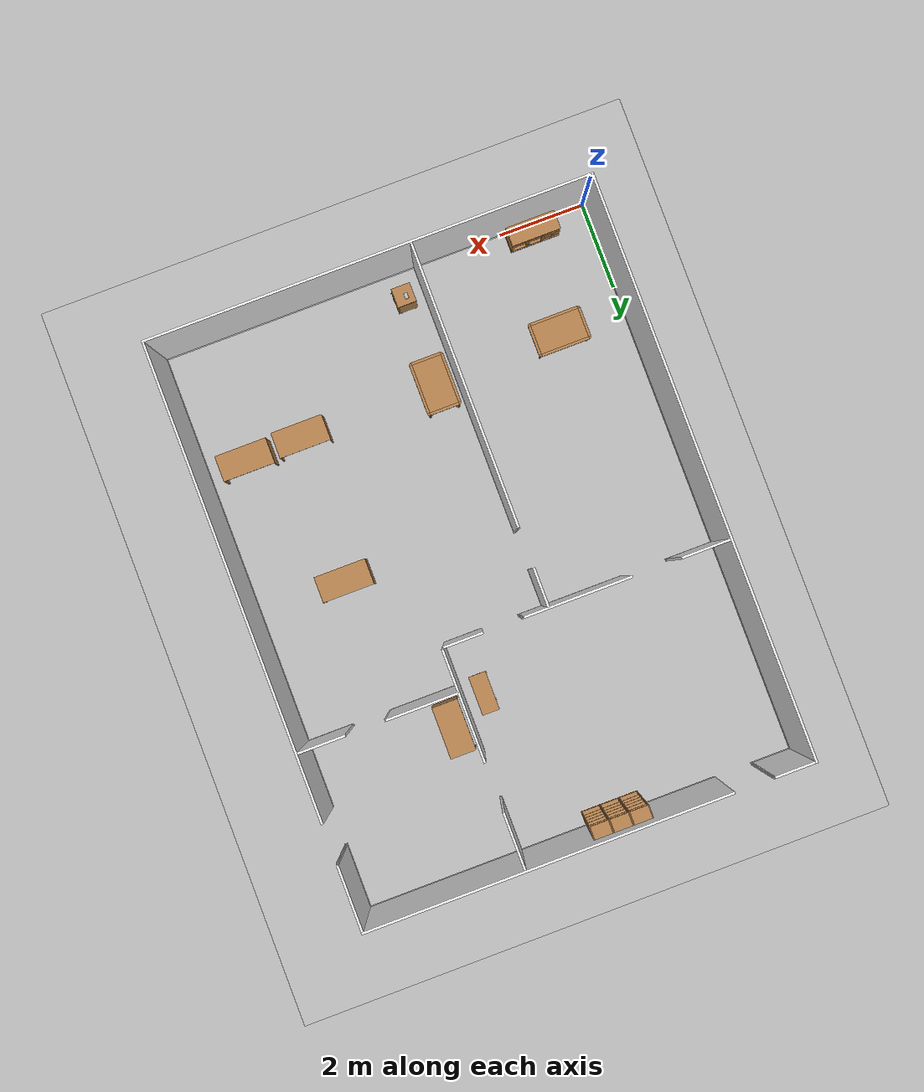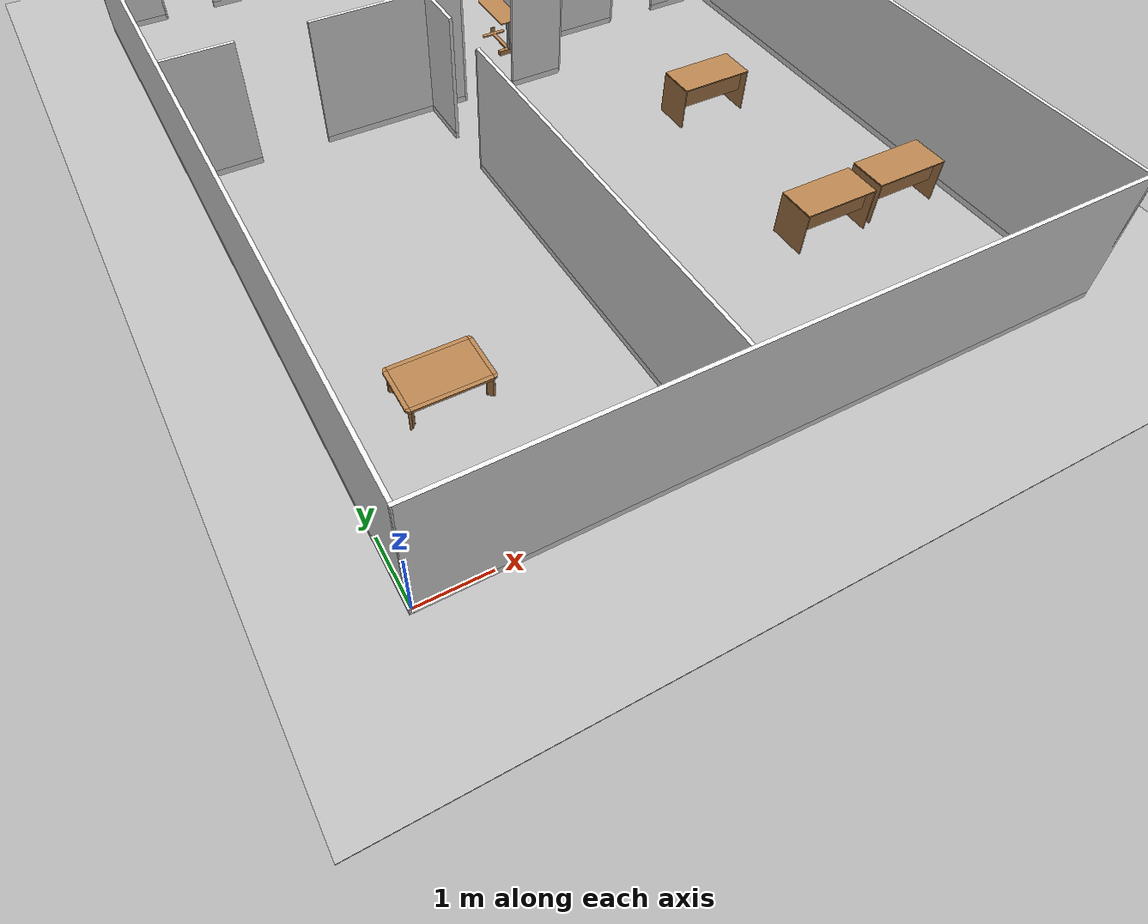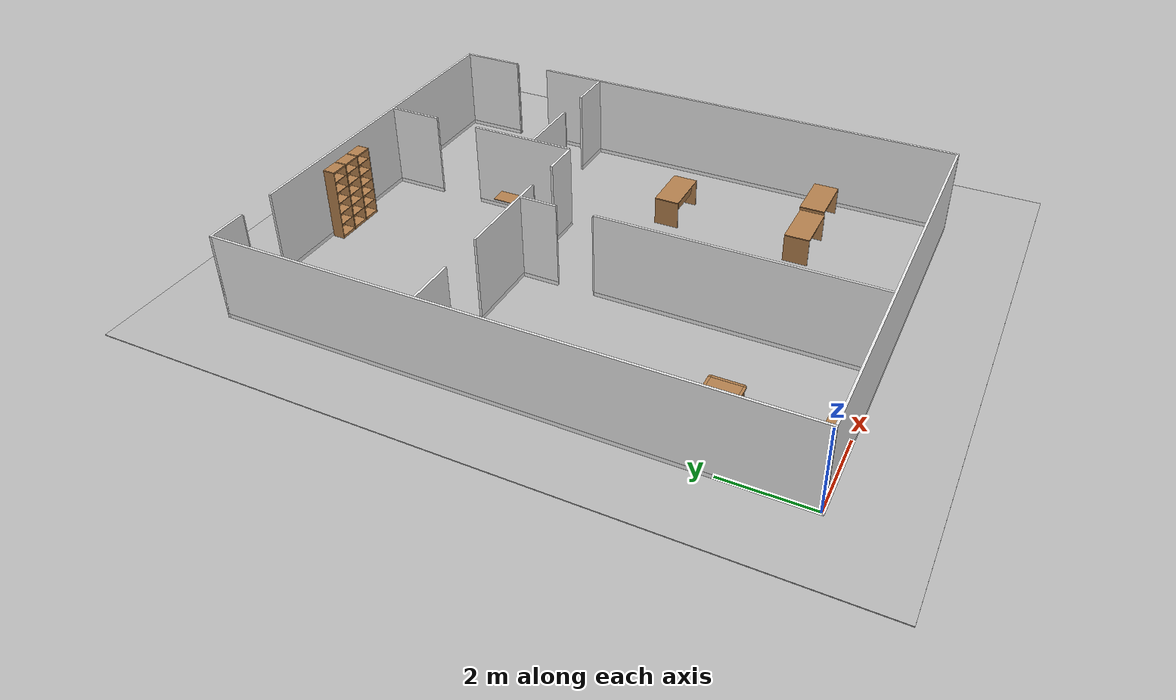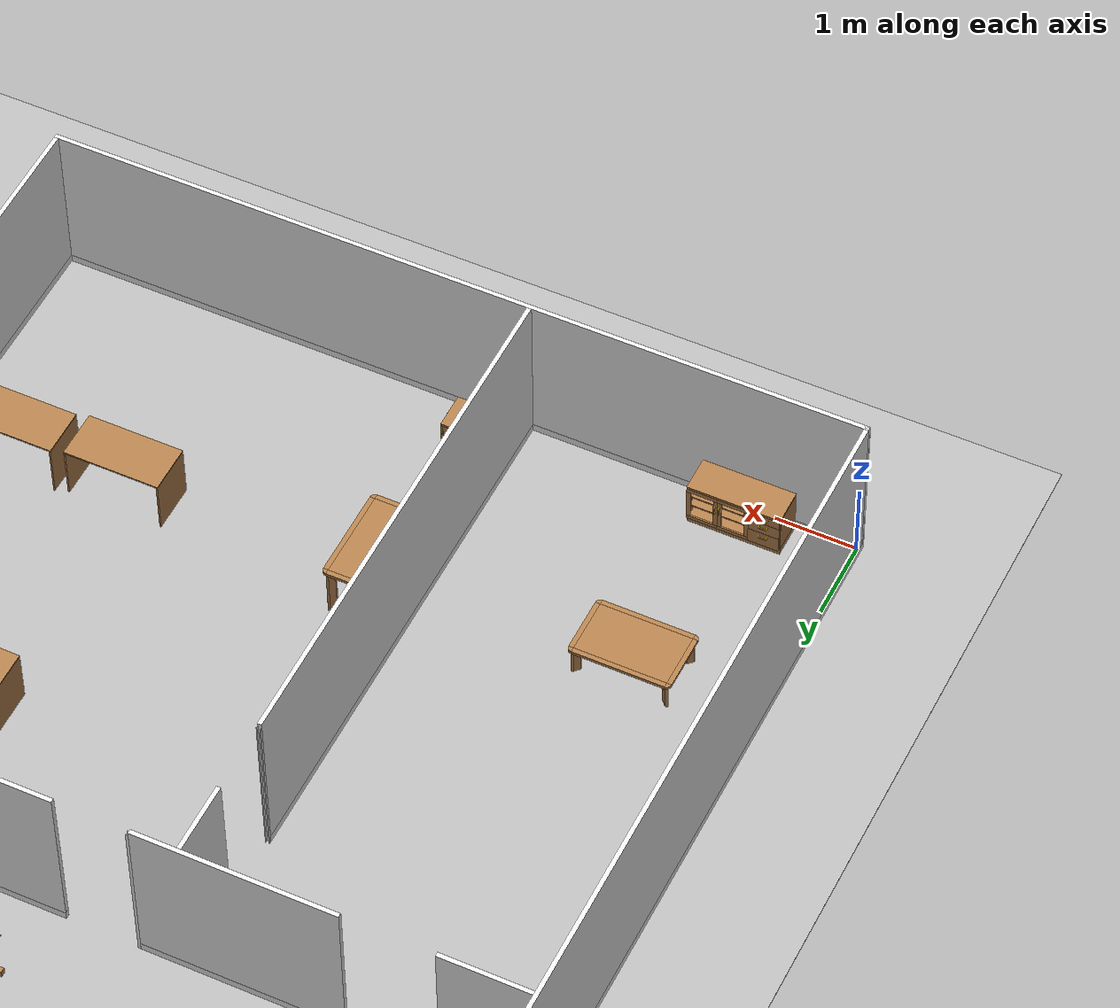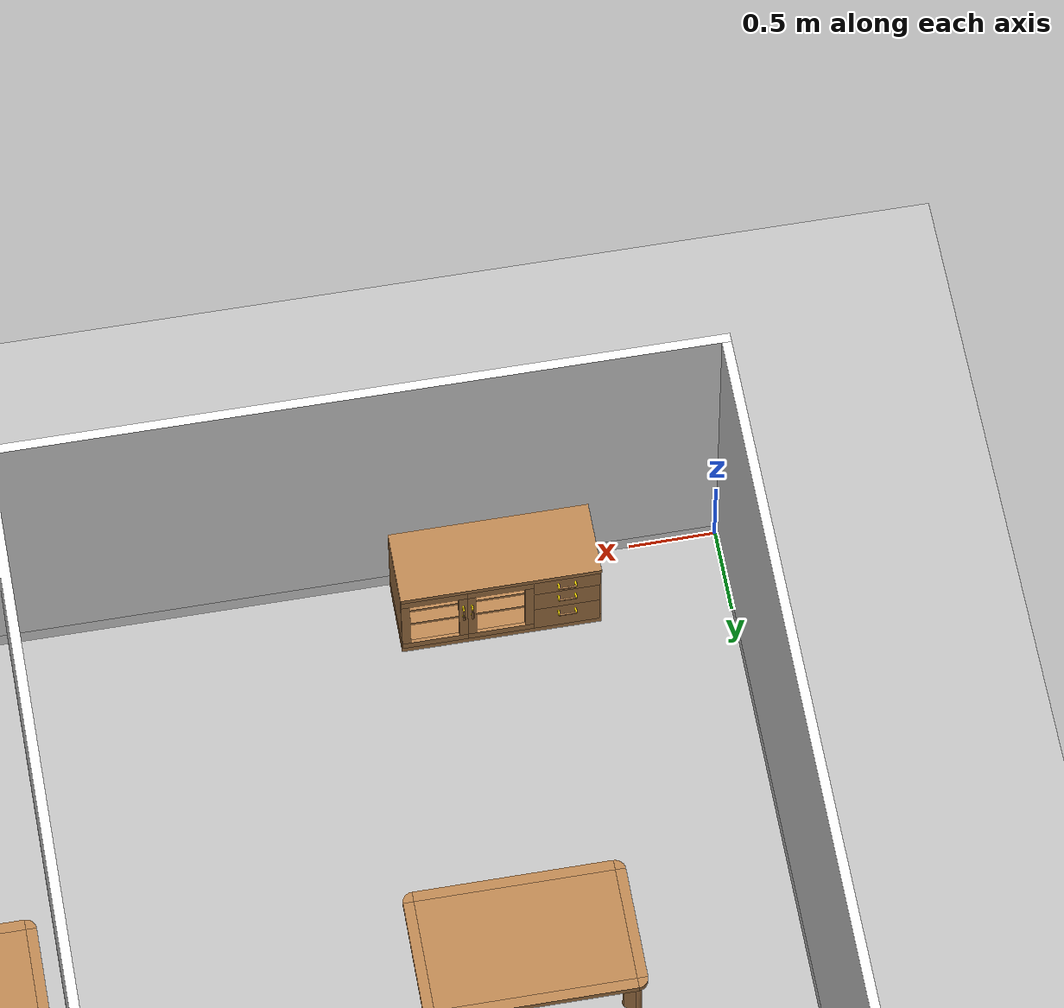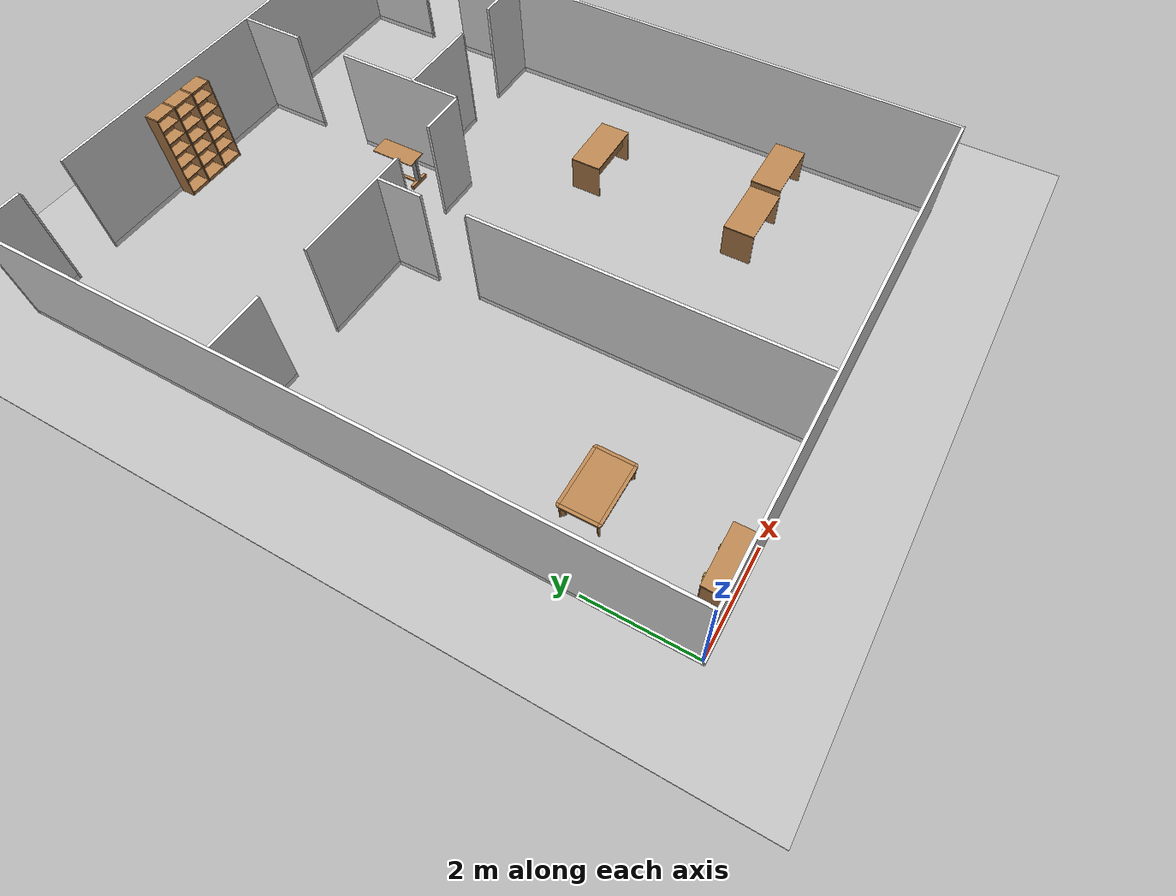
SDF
<sdf version="1.6">
 <world name="default">
  <scene>
   <ambient>0.5 0.5 0.5 1</ambient>
   <shadows>0</shadows>
   <grid>0</grid>
   <background>0.7 0.7 0.7 1</background>
  </scene>
  <physics name="default_physics" default="0" type="ode">
   <max_step_size>0.001</max_step_size>
   <real_time_factor>1</real_time_factor>
   <real_time_update_rate>1000</real_time_update_rate>
  </physics>
  <model name="gplane">
   <pose>5.0375 6.59 0 0 -0 0</pose>
   <link name="body">
    <collision name="gplane_coll">
     <geometry><plane><normal>0 0 1</normal><size>10.075 13.18</size></plane></geometry>
     <surface><contact><ode><kp>1e+06</kp><kd>1</kd></ode></contact></surface>
     <laser_retro>2000</laser_retro>
    </collision>
    <visual name="gplane_vis">
     <geometry><plane><normal>0 0 1</normal><size>10.075 13.18</size></plane></geometry>
     <material>
      <script>
       <uri>model://base_materials/carpet/scripts</uri>
       <uri>model://base_materials/carpet/textures</uri>
       <name>carpet/carpet01</name>
      </script>
     </material>
     <cast_shadows>0</cast_shadows>
    </visual>
    <velocity_decay><linear>0</linear><angular>0</angular></velocity_decay>
   </link>
   <static>1</static>
  </model>
  <light name="inner_point_white1" type="point">
   <pose>4 5 4 0 -0 0</pose>
   <diffuse>0.2 0.2 0.2 1</diffuse>
   <specular>0.1 0.1 0.1 1</specular>
   <attenuation>
    <range>20</range>
    <linear>0.1</linear>
    <constant>0.2</constant>
    <quadratic>0</quadratic>
   </attenuation>
   <cast_shadows>0</cast_shadows>
   <direction>0 0 -1</direction>
  </light>
  <light name="inner_point_white2" type="point">
   <pose>4 10 4 0 -0 0</pose>
   <diffuse>0.2 0.2 0.2 1</diffuse>
   <specular>0.1 0.1 0.1 1</specular>
   <attenuation>
    <range>20</range>
    <linear>0.1</linear>
    <constant>0.2</constant>
    <quadratic>0</quadratic>
   </attenuation>
   <cast_shadows>0</cast_shadows>
   <direction>0 0 -1</direction>
  </light>
  <light name="inner_point_white3" type="point">
   <pose>8 5 4 0 -0 0</pose>
   <diffuse>0.2 0.2 0.2 1</diffuse>
   <specular>0.1 0.1 0.1 1</specular>
   <attenuation>
    <range>20</range>
    <linear>0.1</linear>
    <constant>0.2</constant>
    <quadratic>0</quadratic>
   </attenuation>
   <cast_shadows>0</cast_shadows>
   <direction>0 0 -1</direction>
  </light>
  <light name="inner_point_white4" type="point">
   <pose>8 10 4 0 -0 0</pose>
   <diffuse>0.2 0.2 0.2 1</diffuse>
   <specular>0.1 0.1 0.1 1</specular>
   <attenuation>
    <range>20</range>
    <linear>0.1</linear>
    <constant>0.2</constant>
    <quadratic>0</quadratic>
   </attenuation>
   <cast_shadows>0</cast_shadows>
   <direction>0 0 -1</direction>
  </light>
  <model name="inside_wall">
   <link name="link">
    <inertial>
     <mass>50</mass>
     <inertia><ixx>1</ixx><ixy>0</ixy><ixz>0</ixz><iyy>1</iyy><iyz>0</iyz><izz>1</izz></inertia>
    </inertial>
    <visual name="x05y01_08_bottom_frame">
     <pose>4.075 3.215 0.05 0 -0 0</pose>
     <geometry><box><size>0.055 6.43 0.1</size></box></geometry>
     <material>
      <script><uri>model://base_materials/color/scripts</uri><name>hsr_color/white</name></script>
     </material>
    </visual>
    <collision name="x05y01_08_collision_bottom_frame">
     <pose>4.075 3.215 0.05 0 -0 0</pose>
     <geometry><box><size>0.055 6.43 0.1</size></box></geometry>
    </collision>
    <visual name="x05y01_08_wall">
     <pose>4.075 3.215 1.095 0 -0 0</pose>
     <geometry><box><size>0.055 6.43 1.99</size></box></geometry>
     <material>
      <script>
       <uri>model://base_materials/wall/scripts</uri>
       <uri>model://base_materials/wall/textures</uri>
       <name>wall/white_noise</name>
      </script>
     </material>
    </visual>
    <collision name="x05y01_08_collision_wall">
     <pose>4.075 3.215 1.095 0 -0 0</pose>
     <geometry><box><size>0.055 6.43 1.99</size></box></geometry>
    </collision>
    <visual name="x05y10_bottom_frame">
     <pose>4.075 7.78 0.05 0 -0 0</pose>
     <geometry><box><size>0.055 0.9 0.1</size></box></geometry>
     <material>
      <script><uri>model://base_materials/color/scripts</uri><name>hsr_color/white</name></script>
     </material>
    </visual>
    <collision name="x05y10_collision_bottom_frame">
     <pose>4.075 7.78 0.05 0 -0 0</pose>
     <geometry><box><size>0.055 0.9 0.1</size></box></geometry>
    </collision>
    <visual name="x05y10_wall">
     <pose>4.075 7.78 1.095 0 -0 0</pose>
     <geometry><box><size>0.055 0.9 1.99</size></box></geometry>
     <material>
      <script>
       <uri>model://base_materials/wall/scripts</uri>
       <uri>model://base_materials/wall/textures</uri>
       <name>wall/white_noise</name>
      </script>
     </material>
    </visual>
    <collision name="x05y10_collision_wall">
     <pose>4.075 7.78 1.095 0 -0 0</pose>
     <geometry><box><size>0.055 0.9 1.99</size></box></geometry>
    </collision>
    <visual name="x01_02_y09_bottom_frame">
     <pose>0.55 8.23 0.05 0 -0 1.5708</pose>
     <geometry><box><size>0.055 1.1 0.1</size></box></geometry>
     <material>
      <script><uri>model://base_materials/color/scripts</uri><name>hsr_color/white</name></script>
     </material>
    </visual>
    <collision name="x01_02_y09_collision_bottom_frame">
     <pose>0.55 8.23 0.05 0 -0 1.5708</pose>
     <geometry><box><size>0.055 1.1 0.1</size></box></geometry>
    </collision>
    <visual name="x01_02_y09_wall">
     <pose>0.55 8.23 1.095 0 -0 1.5708</pose>
     <geometry><box><size>0.055 1.1 1.99</size></box></geometry>
     <material>
      <script>
       <uri>model://base_materials/wall/scripts</uri>
       <uri>model://base_materials/wall/textures</uri>
       <name>wall/white_noise</name>
      </script>
     </material>
    </visual>
    <collision name="x01_02_y09_collision_wall">
     <pose>0.55 8.23 1.095 0 -0 1.5708</pose>
     <geometry><box><size>0.055 1.1 1.99</size></box></geometry>
    </collision>
    <visual name="x04_07_y09_bottom_frame">
     <pose>3.42 8.23 0.05 0 -0 1.5708</pose>
     <geometry><box><size>0.055 2.44 0.1</size></box></geometry>
     <material>
      <script><uri>model://base_materials/color/scripts</uri><name>hsr_color/white</name></script>
     </material>
    </visual>
    <collision name="x04_07_y09_collision_bottom_frame">
     <pose>3.42 8.23 0.05 0 -0 1.5708</pose>
     <geometry><box><size>0.055 2.44 0.1</size></box></geometry>
    </collision>
    <visual name="x04_07_y09_wall">
     <pose>3.42 8.23 1.095 0 -0 1.5708</pose>
     <geometry><box><size>0.055 2.44 1.99</size></box></geometry>
     <material>
      <script>
       <uri>model://base_materials/wall/scripts</uri>
       <uri>model://base_materials/wall/textures</uri>
       <name>wall/white_noise</name>
      </script>
     </material>
    </visual>
    <collision name="x04_07_y09_collision_wall">
     <pose>3.42 8.23 1.095 0 -0 1.5708</pose>
     <geometry><box><size>0.055 2.44 1.99</size></box></geometry>
    </collision>
    <visual name="x08y10a_bottom_frame">
     <pose>5.9925 8.23 0.05 0 -0 1.5708</pose>
     <geometry><box><size>0.055 0.9 0.1</size></box></geometry>
     <material>
      <script><uri>model://base_materials/color/scripts</uri><name>hsr_color/white</name></script>
     </material>
    </visual>
    <collision name="x08y10a_collision_bottom_frame">
     <pose>5.9925 8.23 0.05 0 -0 1.5708</pose>
     <geometry><box><size>0.055 0.9 0.1</size></box></geometry>
    </collision>
    <visual name="x08y10a_wall">
     <pose>5.9925 8.23 1.095 0 -0 1.5708</pose>
     <geometry><box><size>0.055 0.9 1.99</size></box></geometry>
     <material>
      <script>
       <uri>model://base_materials/wall/scripts</uri>
       <uri>model://base_materials/wall/textures</uri>
       <name>wall/white_noise</name>
      </script>
     </material>
    </visual>
    <collision name="x08y10a_collision_wall">
     <pose>5.9925 8.23 1.095 0 -0 1.5708</pose>
     <geometry><box><size>0.055 0.9 1.99</size></box></geometry>
    </collision>
    <visual name="x08y10a_bottom_frame">
     <pose>5.9925 8.23 0.05 0 -0 1.5708</pose>
     <geometry><box><size>0.055 0.9 0.1</size></box></geometry>
     <material>
      <script><uri>model://base_materials/color/scripts</uri><name>hsr_color/white</name></script>
     </material>
    </visual>
    <collision name="x08y10a_collision_bottom_frame">
     <pose>5.9925 8.23 0.05 0 -0 1.5708</pose>
     <geometry><box><size>0.055 0.9 0.1</size></box></geometry>
    </collision>
    <visual name="x08y10a_wall">
     <pose>5.9925 8.23 1.095 0 -0 1.5708</pose>
     <geometry><box><size>0.055 0.9 1.99</size></box></geometry>
     <material>
      <script>
       <uri>model://base_materials/wall/scripts</uri>
       <uri>model://base_materials/wall/textures</uri>
       <name>wall/white_noise</name>
      </script>
     </material>
    </visual>
    <collision name="x08y10a_collision_wall">
     <pose>5.9925 8.23 1.095 0 -0 1.5708</pose>
     <geometry><box><size>0.055 0.9 1.99</size></box></geometry>
    </collision>
    <visual name="x08y14_15_bottom_frame">
     <pose>6.47 12.54 0.05 0 -0 0</pose>
     <geometry><box><size>0.055 1.28 0.1</size></box></geometry>
     <material>
      <script><uri>model://base_materials/color/scripts</uri><name>hsr_color/white</name></script>
     </material>
    </visual>
    <collision name="x08y14_15_collision_bottom_frame">
     <pose>6.47 12.54 0.05 0 -0 0</pose>
     <geometry><box><size>0.055 1.28 0.1</size></box></geometry>
    </collision>
    <visual name="x08y14_15_wall">
     <pose>6.47 12.54 1.095 0 -0 0</pose>
     <geometry><box><size>0.055 1.28 1.99</size></box></geometry>
     <material>
      <script>
       <uri>model://base_materials/wall/scripts</uri>
       <uri>model://base_materials/wall/textures</uri>
       <name>wall/white_noise</name>
      </script>
     </material>
    </visual>
    <collision name="x08y14_15_collision_wall">
     <pose>6.47 12.54 1.095 0 -0 0</pose>
     <geometry><box><size>0.055 1.28 1.99</size></box></geometry>
    </collision>
    <visual name="x08y10b_12_bottom_frame">
     <pose>6.47 9.52875 0.05 0 -0 0</pose>
     <geometry><box><size>0.055 2.5425 0.1</size></box></geometry>
     <material>
      <script><uri>model://base_materials/color/scripts</uri><name>hsr_color/white</name></script>
     </material>
    </visual>
    <collision name="x08y10b_12_collision_bottom_frame">
     <pose>6.47 9.52875 0.05 0 -0 0</pose>
     <geometry><box><size>0.055 2.5425 0.1</size></box></geometry>
    </collision>
    <visual name="x08y10b_12_wall">
     <pose>6.47 9.52875 1.095 0 -0 0</pose>
     <geometry><box><size>0.055 2.5425 1.99</size></box></geometry>
     <material>
      <script>
       <uri>model://base_materials/wall/scripts</uri>
       <uri>model://base_materials/wall/textures</uri>
       <name>wall/white_noise</name>
      </script>
     </material>
    </visual>
    <collision name="x08y10b_12_collision_wall">
     <pose>6.47 9.52875 1.095 0 -0 0</pose>
     <geometry><box><size>0.055 2.5425 1.99</size></box></geometry>
    </collision>
    <visual name="x08_09y11b_bottom_frame">
     <pose>7.284 9.23 0.05 0 -0 1.5708</pose>
     <geometry><box><size>0.055 1.632 0.1</size></box></geometry>
     <material>
      <script><uri>model://base_materials/color/scripts</uri><name>hsr_color/white</name></script>
     </material>
    </visual>
    <collision name="x08_09y11b_collision_bottom_frame">
     <pose>7.284 9.23 0.05 0 -0 1.5708</pose>
     <geometry><box><size>0.055 1.632 0.1</size></box></geometry>
    </collision>
    <visual name="x08_09y11b_wall">
     <pose>7.284 9.23 1.095 0 -0 1.5708</pose>
     <geometry><box><size>0.055 1.632 1.99</size></box></geometry>
     <material>
      <script>
       <uri>model://base_materials/wall/scripts</uri>
       <uri>model://base_materials/wall/textures</uri>
       <name>wall/white_noise</name>
      </script>
     </material>
    </visual>
    <collision name="x08_09y11b_collision_wall">
     <pose>7.284 9.23 1.095 0 -0 1.5708</pose>
     <geometry><box><size>0.055 1.632 1.99</size></box></geometry>
    </collision>
    <visual name="x11_12y11_bottom_frame">
     <pose>9.5375 9.23 0.05 0 -0 1.5708</pose>
     <geometry><box><size>0.055 1.075 0.1</size></box></geometry>
     <material>
      <script><uri>model://base_materials/color/scripts</uri><name>hsr_color/white</name></script>
     </material>
    </visual>
    <collision name="x11_12y11_collision_bottom_frame">
     <pose>9.5375 9.23 0.05 0 -0 1.5708</pose>
     <geometry><box><size>0.055 1.075 0.1</size></box></geometry>
    </collision>
    <visual name="x11_12y11_wall">
     <pose>9.5375 9.23 1.095 0 -0 1.5708</pose>
     <geometry><box><size>0.055 1.075 1.99</size></box></geometry>
     <material>
      <script>
       <uri>model://base_materials/wall/scripts</uri>
       <uri>model://base_materials/wall/textures</uri>
       <name>wall/white_noise</name>
      </script>
     </material>
    </visual>
    <collision name="x11_12y11_collision_wall">
     <pose>9.5375 9.23 1.095 0 -0 1.5708</pose>
     <geometry><box><size>0.055 1.075 1.99</size></box></geometry>
    </collision>
    <velocity_decay><linear>0</linear><angular>0</angular></velocity_decay>
   </link>
   <static>1</static>
  </model>
  <model name="outside_wall">
   <link name="link">
    <inertial>
     <mass>50</mass>
     <inertia><ixx>1</ixx><ixy>0</ixy><ixz>0</ixz><iyy>1</iyy><iyz>0</iyz><izz>1</izz></inertia>
    </inertial>
    <visual name="x00_13y00_bottom_frame">
     <pose>5.0375 -0.0275 0.05 0 -0 0</pose>
     <geometry><box><size>10.185 0.055 0.1</size></box></geometry>
     <material>
      <script><uri>model://base_materials/color/scripts</uri><name>hsr_color/white</name></script>
     </material>
    </visual>
    <collision name="x00_13y00_collision_bottom_frame">
     <pose>5.0375 -0.0275 0.05 0 -0 0</pose>
     <geometry><box><size>10.185 0.055 0.1</size></box></geometry>
    </collision>
    <visual name="wall_x00_13y00">
     <pose>5.0375 -0.0275 1.095 0 -0 0</pose>
     <geometry><box><size>10.185 0.055 1.99</size></box></geometry>
     <material>
      <script>
       <uri>model://base_materials/wall/scripts</uri>
       <uri>model://base_materials/wall/textures</uri>
       <name>wall/white_noise</name>
      </script>
     </material>
    </visual>
    <collision name="wall_x00_13y00">
     <pose>5.0375 -0.002 1.095 0 -0 0</pose>
     <geometry><box><size>10.08 0.055 1.99</size></box></geometry>
    </collision>
    <visual name="x00y00_15_bottom_frame">
     <pose>-0.0275 6.59 0.05 0 -0 0</pose>
     <geometry><box><size>0.055 13.29 0.1</size></box></geometry>
     <material>
      <script><uri>model://base_materials/color/scripts</uri><name>hsr_color/white</name></script>
     </material>
    </visual>
    <collision name="x00y00_15_collision_bottom_frame">
     <pose>-0.0275 6.59 0.05 0 -0 0</pose>
     <geometry><box><size>0.055 13.29 0.1</size></box></geometry>
    </collision>
    <visual name="wall_x00y00_15">
     <pose>-0.0275 6.59 1.095 0 -0 0</pose>
     <geometry><box><size>0.055 13.29 1.99</size></box></geometry>
     <material>
      <script>
       <uri>model://base_materials/wall/scripts</uri>
       <uri>model://base_materials/wall/textures</uri>
       <name>wall/white_noise</name>
      </script>
     </material>
    </visual>
    <collision name="wall_x00y00_x00y15">
     <pose>-0.002 6.59 1.095 0 -0 0</pose>
     <geometry><box><size>0.002 13.29 1.99</size></box></geometry>
    </collision>
    <visual name="x13y00_12_bottom_frame">
     <pose>10.1025 5.3725 0.05 0 -0 0</pose>
     <geometry><box><size>0.055 10.855 0.1</size></box></geometry>
     <material>
      <script><uri>model://base_materials/color/scripts</uri><name>hsr_color/white</name></script>
     </material>
    </visual>
    <collision name="x13y00_12_collision_bottom_frame">
     <pose>10.1025 5.3725 0.05 0 -0 0</pose>
     <geometry><box><size>0.055 10.855 0.1</size></box></geometry>
    </collision>
    <visual name="wall_x13y00_12">
     <pose>10.1025 5.3725 1.095 0 -0 0</pose>
     <geometry><box><size>0.055 10.855 1.99</size></box></geometry>
     <material>
      <script>
       <uri>model://base_materials/wall/scripts</uri>
       <uri>model://base_materials/wall/textures</uri>
       <name>wall/white_noise</name>
      </script>
     </material>
    </visual>
    <collision name="wall_x13y00_12">
     <pose>10.1025 5.3725 1.095 0 -0 0</pose>
     <geometry><box><size>0.055 10.855 1.99</size></box></geometry>
    </collision>
    <visual name="x13y14_16_bottom_frame">
     <pose>10.1025 12.4675 0.05 0 -0 0</pose>
     <geometry><box><size>0.055 1.535 0.1</size></box></geometry>
     <material>
      <script><uri>model://base_materials/color/scripts</uri><name>hsr_color/white</name></script>
     </material>
    </visual>
    <collision name="x13y14_16_collision_bottom_frame">
     <pose>10.1025 12.4675 0.05 0 -0 0</pose>
     <geometry><box><size>0.055 1.535 0.1</size></box></geometry>
    </collision>
    <visual name="wall_x13y14_x13y16">
     <pose>10.1025 12.4675 1.095 0 -0 0</pose>
     <geometry><box><size>0.055 1.535 1.99</size></box></geometry>
     <material>
      <script>
       <uri>model://base_materials/wall/scripts</uri>
       <uri>model://base_materials/wall/textures</uri>
       <name>wall/white_noise</name>
      </script>
     </material>
    </visual>
    <collision name="wall_x13y14_x13y16">
     <pose>10.1025 12.4675 1.095 0 -0 0</pose>
     <geometry><box><size>0.055 1.535 1.99</size></box></geometry>
    </collision>
    <visual name="x00_01y16_bottom_frame">
     <pose>0.4225 13.2075 0.05 0 -0 0</pose>
     <geometry><box><size>0.955 0.055 0.1</size></box></geometry>
     <material>
      <script><uri>model://base_materials/color/scripts</uri><name>hsr_color/white</name></script>
     </material>
    </visual>
    <collision name="x00_01y16_collision_bottom_frame">
     <pose>0.4225 13.2075 0.05 0 -0 0</pose>
     <geometry><box><size>0.955 0.055 0.1</size></box></geometry>
    </collision>
    <visual name="wall_x00_01y16">
     <pose>0.4225 13.2075 1.095 0 -0 0</pose>
     <geometry><box><size>0.955 0.055 1.99</size></box></geometry>
     <material>
      <script>
       <uri>model://base_materials/wall/scripts</uri>
       <uri>model://base_materials/wall/textures</uri>
       <name>wall/white_noise</name>
      </script>
     </material>
    </visual>
    <collision name="wall_x00_x01y16">
     <pose>0.4225 13.2075 1.095 0 -0 0</pose>
     <geometry><box><size>0.955 0.055 1.99</size></box></geometry>
    </collision>
    <visual name="x03_13y16_bottom_frame">
     <pose>5.965 13.2075 0.05 0 -0 0</pose>
     <geometry><box><size>8.33 0.05 0.1</size></box></geometry>
     <material>
      <script><uri>model://base_materials/color/scripts</uri><name>hsr_color/white</name></script>
     </material>
    </visual>
    <collision name="x03_13y16_collision_bottom_frame">
     <pose>5.965 13.2075 0.05 0 -0 0</pose>
     <geometry><box><size>8.33 0.05 0.1</size></box></geometry>
    </collision>
    <visual name="wall_x03_13y16">
     <pose>5.965 13.2075 1.095 0 -0 0</pose>
     <geometry><box><size>8.33 0.055 1.99</size></box></geometry>
     <material>
      <script>
       <uri>model://base_materials/wall/scripts</uri>
       <uri>model://base_materials/wall/textures</uri>
       <name>wall/white_noise</name>
      </script>
     </material>
    </visual>
    <collision name="wall_x03_13y16">
     <pose>5.965 13.2075 1.095 0 -0 0</pose>
     <geometry><box><size>8.33 0.055 1.99</size></box></geometry>
    </collision>
    <velocity_decay><linear>0</linear><angular>0</angular></velocity_decay>
   </link>
   <static>1</static>
  </model>
  <model name="door_stopper_x13y13">
   <link name="door_frame">
    <visual name="stopper">
     <pose>0.0225 0.0175 1.025 0 -0 0</pose>
     <geometry><box><size>0.01 0.035 2.05</size></box></geometry>
     <material>
      <script><uri>model://base_materials/color/scripts</uri><name>hsr_color/white</name></script>
     </material>
    </visual>
    <collision name="collision_frame_1">
     <pose>0.0225 0.0175 1.025 0 -0 0</pose>
     <geometry><box><size>0.01 0.035 2.05</size></box></geometry>
    </collision>
    <visual name="frame_2">
     <pose>-0.0225 0.0175 1.025 0 -0 0</pose>
     <geometry><box><size>0.01 0.035 2.05</size></box></geometry>
     <material>
      <script><uri>model://base_materials/color/scripts</uri><name>hsr_color/white</name></script>
     </material>
    </visual>
    <collision name="collision_frame_2">
     <pose>-0.0225 0.0175 1.025 0 -0 0</pose>
     <geometry><box><size>0.01 0.035 2.05</size></box></geometry>
    </collision>
   </link>
   <static>1</static>
   <pose>10.1025 11.67 0 0 -0 0</pose>
  </model>
  <model name="door_stopper_x02y16">
   <link name="door_frame">
    <visual name="stopper">
     <pose>0.0225 0.0175 1.025 0 -0 0</pose>
     <geometry><box><size>0.01 0.035 2.05</size></box></geometry>
     <material>
      <script><uri>model://base_materials/color/scripts</uri><name>hsr_color/white</name></script>
     </material>
    </visual>
    <collision name="collision_frame_1">
     <pose>0.0225 0.0175 1.025 0 -0 0</pose>
     <geometry><box><size>0.01 0.035 2.05</size></box></geometry>
    </collision>
    <visual name="frame_2">
     <pose>-0.0225 0.0175 1.025 0 -0 0</pose>
     <geometry><box><size>0.01 0.035 2.05</size></box></geometry>
     <material>
      <script><uri>model://base_materials/color/scripts</uri><name>hsr_color/white</name></script>
     </material>
    </visual>
    <collision name="collision_frame_2">
     <pose>-0.0225 0.0175 1.025 0 -0 0</pose>
     <geometry><box><size>0.01 0.035 2.05</size></box></geometry>
    </collision>
   </link>
   <static>1</static>
   <pose>0.93 13.2075 0 0 -0 1.5708</pose>
  </model>
  <model name="door_stopper_x05y09a">
   <link name="door_frame">
    <visual name="stopper">
     <pose>0.0225 0.0175 1.025 0 -0 0</pose>
     <geometry><box><size>0.01 0.035 2.05</size></box></geometry>
     <material>
      <script><uri>model://base_materials/color/scripts</uri><name>hsr_color/white</name></script>
     </material>
    </visual>
    <collision name="collision_frame_1">
     <pose>0.0225 0.0175 1.025 0 -0 0</pose>
     <geometry><box><size>0.01 0.035 2.05</size></box></geometry>
    </collision>
    <visual name="frame_2">
     <pose>-0.0225 0.0175 1.025 0 -0 0</pose>
     <geometry><box><size>0.01 0.035 2.05</size></box></geometry>
     <material>
      <script><uri>model://base_materials/color/scripts</uri><name>hsr_color/white</name></script>
     </material>
    </visual>
    <collision name="collision_frame_2">
     <pose>-0.0225 0.0175 1.025 0 -0 0</pose>
     <geometry><box><size>0.01 0.035 2.05</size></box></geometry>
    </collision>
   </link>
   <static>1</static>
   <pose>4.075 6.425 0 0 -0 0</pose>
  </model>
  <model name="door_stopper_x08y09a">
   <link name="door_frame">
    <visual name="stopper">
     <pose>0.0225 0.0175 1.025 0 -0 0</pose>
     <geometry><box><size>0.01 0.035 2.05</size></box></geometry>
     <material>
      <script><uri>model://base_materials/color/scripts</uri><name>hsr_color/white</name></script>
     </material>
    </visual>
    <collision name="collision_frame_1">
     <pose>0.0225 0.0175 1.025 0 -0 0</pose>
     <geometry><box><size>0.01 0.035 2.05</size></box></geometry>
    </collision>
    <visual name="frame_2">
     <pose>-0.0225 0.0175 1.025 0 -0 0</pose>
     <geometry><box><size>0.01 0.035 2.05</size></box></geometry>
     <material>
      <script><uri>model://base_materials/color/scripts</uri><name>hsr_color/white</name></script>
     </material>
    </visual>
    <collision name="collision_frame_2">
     <pose>-0.0225 0.0175 1.025 0 -0 0</pose>
     <geometry><box><size>0.01 0.035 2.05</size></box></geometry>
    </collision>
   </link>
   <static>1</static>
   <pose>4.675 8.23 0 0 -0 1.5708</pose>
  </model>
  <model name="door_stopper_x10y11">
   <link name="door_frame">
    <visual name="stopper">
     <pose>0.0225 0.0175 1.025 0 -0 0</pose>
     <geometry><box><size>0.01 0.035 2.05</size></box></geometry>
     <material>
      <script><uri>model://base_materials/color/scripts</uri><name>hsr_color/white</name></script>
     </material>
    </visual>
    <collision name="collision_frame_1">
     <pose>0.0225 0.0175 1.025 0 -0 0</pose>
     <geometry><box><size>0.01 0.035 2.05</size></box></geometry>
    </collision>
    <visual name="frame_2">
     <pose>-0.0225 0.0175 1.025 0 -0 0</pose>
     <geometry><box><size>0.01 0.035 2.05</size></box></geometry>
     <material>
      <script><uri>model://base_materials/color/scripts</uri><name>hsr_color/white</name></script>
     </material>
    </visual>
    <collision name="collision_frame_2">
     <pose>-0.0225 0.0175 1.025 0 -0 0</pose>
     <geometry><box><size>0.01 0.035 2.05</size></box></geometry>
    </collision>
   </link>
   <static>1</static>
   <pose>8.13 9.23 0 0 -0 1.5708</pose>
  </model>
  <model name="wagon">
   <link name="link">
    <inertial>
     <mass>10</mass>
     <inertia><ixx>1</ixx><ixy>0</ixy><ixz>0</ixz><iyy>1</iyy><iyz>0</iyz><izz>1</izz></inertia>
    </inertial>
    <visual name="left_board">
     <pose>-0.2325 0.01 0.345 0 -0 0</pose>
     <geometry><box><size>0.415 0.02 0.59</size></box></geometry>
     <material>
      <script><uri>model://base_materials/wood/scripts/wood.material</uri><name>base_materials/wood</name></script>
     </material>
    </visual>
    <collision name="collision_left_board">
     <pose>-0.2325 0.01 0.345 0 -0 0</pose>
     <geometry><box><size>0.415 0.02 0.59</size></box></geometry>
    </collision>
    <visual name="right_board">
     <pose>-0.2325 0.4325 0.345 0 -0 0</pose>
     <geometry><box><size>0.415 0.02 0.59</size></box></geometry>
     <material>
      <script><uri>model://base_materials/wood/scripts/wood.material</uri><name>base_materials/wood</name></script>
     </material>
    </visual>
    <collision name="collision_right_board">
     <pose>-0.2325 0.4325 0.345 0 -0 0</pose>
     <geometry><box><size>0.415 0.02 0.59</size></box></geometry>
    </collision>
    <visual name="top_board">
     <pose>-0.22 0.2225 0.655 0 -0 0</pose>
     <geometry><box><size>0.44 0.445 0.03</size></box></geometry>
     <material>
      <script><uri>model://base_materials/wood/scripts/wood.material</uri><name>base_materials/wood</name></script>
     </material>
    </visual>
    <collision name="collision_top_board">
     <pose>-0.22 0.2225 0.655 0 -0 0</pose>
     <geometry><box><size>0.44 0.445 0.03</size></box></geometry>
    </collision>
    <visual name="back_board">
     <pose>-0.425 0.2225 0.345 0 -0 0</pose>
     <geometry><box><size>0.02 0.405 0.59</size></box></geometry>
     <material>
      <script><uri>model://base_materials/wood/scripts/wood.material</uri><name>base_materials/wood</name></script>
     </material>
    </visual>
    <collision name="collision_back_board">
     <pose>-0.425 0.2225 0.345 0 -0 0</pose>
     <geometry><box><size>0.02 0.405 0.59</size></box></geometry>
    </collision>
    <visual name="bottom_board">
     <pose>-0.2325 0.2225 0.06 0 -0 0</pose>
     <geometry><box><size>0.415 0.405 0.02</size></box></geometry>
     <material>
      <script><uri>model://base_materials/wood/scripts/wood.material</uri><name>base_materials/wood</name></script>
     </material>
    </visual>
    <collision name="collision_bottom_board">
     <pose>-0.2325 0.2225 0.06 0 -0 0</pose>
     <geometry><box><size>0.415 0.405 0.02</size></box></geometry>
    </collision>
    <visual name="1st_drawer">
     <pose>-0.0125 0.2225 0.57 0 -0 0</pose>
     <geometry><box><size>0.025 0.445 0.14</size></box></geometry>
     <material>
      <script><uri>model://base_materials/wood/scripts/wood.material</uri><name>base_materials/wood</name></script>
     </material>
    </visual>
    <collision name="collision_1st_drawer">
     <pose>-0.0125 0.2225 0.57 0 -0 0</pose>
     <geometry><box><size>0.025 0.445 0.14</size></box></geometry>
    </collision>
    <visual name="1st_drawer_handle_l1">
     <pose>0.0115 0.1895 0.6 3.14159 1.57079 3.14159</pose>
     <geometry><cylinder><radius>0.007</radius><length>0.023</length></cylinder></geometry>
     <material>
      <ambient>0.18431 0.3098 0.3098 1</ambient>
      <diffuse>0.18431 0.3098 0.3098 1</diffuse>
      <specular>0.1 0.1 0.1 1</specular>
     </material>
    </visual>
    <collision name="collision_1st_drawer_handle_l1">
     <pose>0.0115 0.1895 0.6 3.14159 1.57079 3.14159</pose>
     <geometry><cylinder><radius>0.007</radius><length>0.023</length></cylinder></geometry>
    </collision>
    <visual name="1st_drawer_handle_l2">
     <pose>0.023 0.1895 0.6 0 -0 0</pose>
     <geometry><sphere><radius>0.007</radius></sphere></geometry>
     <material>
      <ambient>0.18431 0.3098 0.3098 1</ambient>
      <diffuse>0.18431 0.3098 0.3098 1</diffuse>
      <specular>0.1 0.1 0.1 1</specular>
     </material>
    </visual>
    <collision name="collision_1st_drawer_handle_l2">
     <pose>0.023 0.1895 0.6 0 -0 0</pose>
     <geometry><sphere><radius>0.007</radius></sphere></geometry>
    </collision>
    <visual name="1st_drawer_handle_r1">
     <pose>0.0115 0.2555 0.6 3.14159 1.57079 3.14159</pose>
     <geometry><cylinder><radius>0.007</radius><length>0.023</length></cylinder></geometry>
     <material>
      <ambient>0.18431 0.3098 0.3098 1</ambient>
      <diffuse>0.18431 0.3098 0.3098 1</diffuse>
      <specular>0.1 0.1 0.1 1</specular>
     </material>
    </visual>
    <collision name="collision_1st_drawer_handle_r1">
     <pose>0.0115 0.2555 0.6 3.14159 1.57079 3.14159</pose>
     <geometry><cylinder><radius>0.007</radius><length>0.023</length></cylinder></geometry>
    </collision>
    <visual name="1st_drawer_handle_r2">
     <pose>0.023 0.2555 0.6 0 -0 0</pose>
     <geometry><sphere><radius>0.007</radius></sphere></geometry>
     <material>
      <ambient>0.18431 0.3098 0.3098 1</ambient>
      <diffuse>0.18431 0.3098 0.3098 1</diffuse>
      <specular>0.1 0.1 0.1 1</specular>
     </material>
    </visual>
    <collision name="collision_1st_drawer_handle_r2">
     <pose>0.023 0.2555 0.6 0 -0 0</pose>
     <geometry><sphere><radius>0.007</radius></sphere></geometry>
    </collision>
    <visual name="1st_drawer_handle_center">
     <pose>0.023 0.2225 0.6 1.5708 -0 0</pose>
     <geometry><cylinder><radius>0.007</radius><length>0.066</length></cylinder></geometry>
     <material>
      <ambient>0.18431 0.3098 0.3098 1</ambient>
      <diffuse>0.18431 0.3098 0.3098 1</diffuse>
      <specular>0.1 0.1 0.1 1</specular>
     </material>
    </visual>
    <collision name="collision_1st_drawer_handle_center">
     <pose>0.023 0.2225 0.6 1.5708 -0 0</pose>
     <geometry><cylinder><radius>0.007</radius><length>0.066</length></cylinder></geometry>
    </collision>
    <visual name="2nd_drawer">
     <pose>-0.0125 0.2225 0.275 0 -0 0</pose>
     <geometry><box><size>0.025 0.445 0.45</size></box></geometry>
     <material>
      <script><uri>model://base_materials/wood/scripts/wood.material</uri><name>base_materials/wood</name></script>
     </material>
    </visual>
    <collision name="collision_2nd_drawer">
     <pose>-0.0125 0.2225 0.275 0 -0 0</pose>
     <geometry><box><size>0.025 0.445 0.45</size></box></geometry>
    </collision>
    <visual name="2nd_drawer_handle_top1">
     <pose>0.0115 0.04 0.47 3.14159 1.57079 3.14159</pose>
     <geometry><cylinder><radius>0.007</radius><length>0.023</length></cylinder></geometry>
     <material>
      <ambient>0.18431 0.3098 0.3098 1</ambient>
      <diffuse>0.18431 0.3098 0.3098 1</diffuse>
      <specular>0.1 0.1 0.1 1</specular>
     </material>
    </visual>
    <collision name="collision_2nd_drawer_handle_top1">
     <pose>0.0115 0.04 0.47 3.14159 1.57079 3.14159</pose>
     <geometry><cylinder><radius>0.007</radius><length>0.023</length></cylinder></geometry>
    </collision>
    <visual name="2nd_drawer_handle_top2">
     <pose>0.023 0.04 0.47 0 -0 0</pose>
     <geometry><sphere><radius>0.007</radius></sphere></geometry>
     <material>
      <ambient>0.18431 0.3098 0.3098 1</ambient>
      <diffuse>0.18431 0.3098 0.3098 1</diffuse>
      <specular>0.1 0.1 0.1 1</specular>
     </material>
    </visual>
    <collision name="2nd_drawer_handle_top2">
     <pose>0.023 0.04 0.47 0 -0 0</pose>
     <geometry><sphere><radius>0.007</radius></sphere></geometry>
    </collision>
    <visual name="2nd_drawer_handle_bottom1">
     <pose>0.0115 0.04 0.404 3.14159 1.57079 3.14159</pose>
     <geometry><cylinder><radius>0.007</radius><length>0.023</length></cylinder></geometry>
     <material>
      <ambient>0.18431 0.3098 0.3098 1</ambient>
      <diffuse>0.18431 0.3098 0.3098 1</diffuse>
      <specular>0.1 0.1 0.1 1</specular>
     </material>
    </visual>
    <collision name="collision_2nd_drawer_handle_bottom1">
     <pose>0.0115 0.04 0.404 3.14159 1.57079 3.14159</pose>
     <geometry><cylinder><radius>0.007</radius><length>0.023</length></cylinder></geometry>
    </collision>
    <visual name="2nd_drawer_handle_bottom2">
     <pose>0.023 0.04 0.404 0 -0 0</pose>
     <geometry><sphere><radius>0.007</radius></sphere></geometry>
     <material>
      <ambient>0.18431 0.3098 0.3098 1</ambient>
      <diffuse>0.18431 0.3098 0.3098 1</diffuse>
      <specular>0.1 0.1 0.1 1</specular>
     </material>
    </visual>
    <collision name="2nd_drawer_handle_bottom2">
     <pose>0.023 0.04 0.404 0 -0 0</pose>
     <geometry><sphere><radius>0.007</radius></sphere></geometry>
    </collision>
    <visual name="2nd_drawer_handle_center">
     <pose>0.023 0.04 0.437 0 -0 0</pose>
     <geometry><cylinder><radius>0.007</radius><length>0.066</length></cylinder></geometry>
     <material>
      <ambient>0.18431 0.3098 0.3098 1</ambient>
      <diffuse>0.18431 0.3098 0.3098 1</diffuse>
      <specular>0.1 0.1 0.1 1</specular>
     </material>
    </visual>
    <collision name="collision_2nd_drawer_handle_center">
     <pose>0.023 0.04 0.437 0 -0 0</pose>
     <geometry><cylinder><radius>0.007</radius><length>0.066</length></cylinder></geometry>
    </collision>
    <visual name="left_front_caster">
     <pose>-0.07 0.025 0.025 3.14159 1.57079 3.14159</pose>
     <geometry><cylinder><radius>0.025</radius><length>0.035</length></cylinder></geometry>
     <material><script><name>Gazebo/Black</name><uri>__default__</uri></script></material>
    </visual>
    <collision name="collision_left_front_caster">
     <pose>-0.07 0.025 0.025 3.14159 1.57079 3.14159</pose>
     <geometry><cylinder><radius>0.025</radius><length>0.035</length></cylinder></geometry>
    </collision>
    <visual name="right_front_caster">
     <pose>-0.07 0.42 0.025 3.14159 1.57079 3.14159</pose>
     <geometry><cylinder><radius>0.025</radius><length>0.035</length></cylinder></geometry>
     <material><script><name>Gazebo/Black</name><uri>__default__</uri></script></material>
    </visual>
    <collision name="collision_right_front_caster">
     <pose>-0.07 0.42 0.025 3.14159 1.57079 3.14159</pose>
     <geometry><cylinder><radius>0.025</radius><length>0.035</length></cylinder></geometry>
    </collision>
    <visual name="left_back_caster">
     <pose>-0.39 0.025 0.025 3.14159 1.57079 3.14159</pose>
     <geometry><cylinder><radius>0.025</radius><length>0.035</length></cylinder></geometry>
     <material><script><name>Gazebo/Black</name><uri>__default__</uri></script></material>
    </visual>
    <collision name="collision_left_back_caster">
     <pose>-0.39 0.025 0.025 3.14159 1.57079 3.14159</pose>
     <geometry><cylinder><radius>0.025</radius><length>0.035</length></cylinder></geometry>
    </collision>
    <visual name="right_back_caster">
     <pose>-0.39 0.42 0.025 3.14159 1.57079 3.14159</pose>
     <geometry><cylinder><radius>0.025</radius><length>0.035</length></cylinder></geometry>
     <material><script><name>Gazebo/Black</name><uri>__default__</uri></script></material>
    </visual>
    <collision name="collision_right_back_caster">
     <pose>-0.39 0.42 0.025 3.14159 1.57079 3.14159</pose>
     <geometry><cylinder><radius>0.025</radius><length>0.035</length></cylinder></geometry>
    </collision>
    <velocity_decay><linear>0</linear><angular>0</angular></velocity_decay>
   </link>
   <static>1</static>
   <pose>4.77681 0.429248 0 0 -0 0</pose>
  </model>
  <model name="nasal_cupsul">
   <link name="link">
    <inertial>
     <mass>0.1</mass>
     <inertia><ixx>0.0001</ixx><ixy>0</ixy><ixz>0</ixz><iyy>0.0001</iyy><iyz>0</iyz><izz>0.0001</izz></inertia>
    </inertial>
    <visual name="capsul">
     <geometry><box><size>0.083 0.135 0.026</size></box></geometry>
     <material>
      <script>
       <uri>model://nasal_inflammation_capsul/scripts</uri>
       <uri>model://nasal_inflammation_capsul/textures</uri>
       <name>oral_medicine/nasal_inflammation_capsule</name>
      </script>
     </material>
    </visual>
    <collision name="collision_capsul">
     <geometry><box><size>0.083 0.135 0.026</size></box></geometry>
     <surface>
      <bounce><restitution_coefficient>0.2</restitution_coefficient><threshold>0</threshold></bounce>
      <contact><ode><max_vel>10</max_vel></ode></contact>
     </surface>
    </collision>
    <velocity_decay><linear>0</linear><angular>0</angular></velocity_decay>
   </link>
   <static>0</static>
   <pose>4.51059 0.687683 0.683 0 0 -0.00012</pose>
  </model>
  <model name="kitchen_lowtable">
   <link name="link">
    <inertial>
     <mass>10</mass>
     <inertia><ixx>1</ixx><ixy>0</ixy><ixz>0</ixz><iyy>1</iyy><iyz>0</iyz><izz>1</izz></inertia>
    </inertial>
    <visual name="center_board">
     <pose>0 0 0.38 0 -0 0</pose>
     <geometry><box><size>0.68 1.13 0.04</size></box></geometry>
     <material>
      <script><uri>model://base_materials/wood/scripts/wood.material</uri><name>base_materials/wood</name></script>
     </material>
    </visual>
    <collision name="collision_center_board">
     <pose>0 0 0.38 0 -0 0</pose>
     <geometry><box><size>0.68 1.13 0.04</size></box></geometry>
    </collision>
    <visual name="front_board">
     <pose>0.37 0 0.38 0 -0 0</pose>
     <geometry><box><size>0.06 1.13 0.04</size></box></geometry>
     <material>
      <script><uri>model://base_materials/wood/scripts/wood.material</uri><name>base_materials/wood</name></script>
     </material>
    </visual>
    <collision name="collision_front_board">
     <pose>0.37 0 0.38 0 -0 0</pose>
     <geometry><box><size>0.06 1.13 0.04</size></box></geometry>
    </collision>
    <visual name="back_board">
     <pose>-0.37 0 0.38 0 -0 0</pose>
     <geometry><box><size>0.06 1.13 0.04</size></box></geometry>
     <material>
      <script><uri>model://base_materials/wood/scripts/wood.material</uri><name>base_materials/wood</name></script>
     </material>
    </visual>
    <collision name="collision_back_board">
     <pose>-0.37 0 0.38 0 -0 0</pose>
     <geometry><box><size>0.06 1.13 0.04</size></box></geometry>
    </collision>
    <visual name="right_board">
     <pose>0 0.595 0.38 0 -0 0</pose>
     <geometry><box><size>0.68 0.06 0.04</size></box></geometry>
     <material>
      <script><uri>model://base_materials/wood/scripts/wood.material</uri><name>base_materials/wood</name></script>
     </material>
    </visual>
    <collision name="collision_right_board">
     <pose>0 0.595 0.38 0 -0 0</pose>
     <geometry><box><size>0.68 0.06 0.04</size></box></geometry>
    </collision>
    <visual name="left_board">
     <pose>0 -0.595 0.38 0 -0 0</pose>
     <geometry><box><size>0.68 0.06 0.04</size></box></geometry>
     <material>
      <script><uri>model://base_materials/wood/scripts/wood.material</uri><name>base_materials/wood</name></script>
     </material>
    </visual>
    <collision name="collision_left_board">
     <pose>0 -0.595 0.38 0 -0 0</pose>
     <geometry><box><size>0.68 0.06 0.04</size></box></geometry>
    </collision>
    <visual name="front_right_corner_board">
     <pose>0.34 0.565 0.38 0 -0 0</pose>
     <geometry><cylinder><radius>0.06</radius><length>0.039</length></cylinder></geometry>
     <material>
      <script><uri>model://base_materials/wood/scripts/wood.material</uri><name>base_materials/wood</name></script>
     </material>
    </visual>
    <collision name="collision_front_right_corner_board">
     <pose>0.34 0.565 0.38 0 -0 0</pose>
     <geometry><cylinder><radius>0.06</radius><length>0.039</length></cylinder></geometry>
    </collision>
    <visual name="front_left_corner_board">
     <pose>0.34 -0.565 0.38 0 -0 0</pose>
     <geometry><cylinder><radius>0.06</radius><length>0.039</length></cylinder></geometry>
     <material>
      <script><uri>model://base_materials/wood/scripts/wood.material</uri><name>base_materials/wood</name></script>
     </material>
    </visual>
    <collision name="collision_front_left_corner_board">
     <pose>0.34 -0.565 0.38 0 -0 0</pose>
     <geometry><cylinder><radius>0.06</radius><length>0.039</length></cylinder></geometry>
    </collision>
    <visual name="front_back_right_corner_board">
     <pose>-0.34 0.565 0.38 0 -0 0</pose>
     <geometry><cylinder><radius>0.06</radius><length>0.039</length></cylinder></geometry>
     <material>
      <script><uri>model://base_materials/wood/scripts/wood.material</uri><name>base_materials/wood</name></script>
     </material>
    </visual>
    <collision name="collision_back_right_corner_board">
     <pose>-0.34 0.565 0.38 0 -0 0</pose>
     <geometry><cylinder><radius>0.06</radius><length>0.039</length></cylinder></geometry>
    </collision>
    <visual name="front_back_left_corner_board">
     <pose>-0.34 -0.565 0.38 0 -0 0</pose>
     <geometry><cylinder><radius>0.06</radius><length>0.039</length></cylinder></geometry>
     <material>
      <script><uri>model://base_materials/wood/scripts/wood.material</uri><name>base_materials/wood</name></script>
     </material>
    </visual>
    <collision name="collision_back_left_corner_board">
     <pose>-0.34 -0.565 0.38 0 -0 0</pose>
     <geometry><cylinder><radius>0.06</radius><length>0.039</length></cylinder></geometry>
    </collision>
    <visual name="front_left_corner_frame1">
     <pose>0.345858 -0.57086 0.18 0 -0 0</pose>
     <geometry><cylinder><radius>0.02</radius><length>0.36</length></cylinder></geometry>
     <material>
      <script><uri>model://base_materials/wood/scripts/wood.material</uri><name>base_materials/wood</name></script>
     </material>
    </visual>
    <collision name="collision_front_left_corner_frame1">
     <pose>0.345858 -0.57086 0.18 0 -0 0</pose>
     <geometry><cylinder><radius>0.02</radius><length>0.36</length></cylinder></geometry>
    </collision>
    <visual name="front_left_corner_frame2">
     <pose>0.317574 -0.54257 0.18 0 -0 0.7854</pose>
     <geometry><box><size>0.04 0.08 0.36</size></box></geometry>
     <material>
      <script><uri>model://base_materials/wood/scripts/wood.material</uri><name>base_materials/wood</name></script>
     </material>
    </visual>
    <collision name="collision_front_left_corner_frame2">
     <pose>0.317574 -0.54257 0.18 0 -0 0.7854</pose>
     <geometry><box><size>0.04 0.08 0.36</size></box></geometry>
    </collision>
    <visual name="front_left_corner_frame3">
     <pose>0.289289 -0.51429 0.18 0 -0 0</pose>
     <geometry><cylinder><radius>0.02</radius><length>0.36</length></cylinder></geometry>
     <material>
      <script><uri>model://base_materials/wood/scripts/wood.material</uri><name>base_materials/wood</name></script>
     </material>
    </visual>
    <collision name="collision_front_left_corner_frame3">
     <pose>0.289289 -0.51429 0.18 0 -0 0</pose>
     <geometry><cylinder><radius>0.02</radius><length>0.36</length></cylinder></geometry>
    </collision>
    <visual name="front_right_corner_frame1">
     <pose>0.345858 0.57086 0.18 0 -0 0</pose>
     <geometry><cylinder><radius>0.02</radius><length>0.36</length></cylinder></geometry>
     <material>
      <script><uri>model://base_materials/wood/scripts/wood.material</uri><name>base_materials/wood</name></script>
     </material>
    </visual>
    <collision name="collision_front_right_corner_frame1">
     <pose>0.345858 0.57086 0.18 0 -0 0</pose>
     <geometry><cylinder><radius>0.02</radius><length>0.36</length></cylinder></geometry>
    </collision>
    <visual name="front_right_corner_frame2">
     <pose>0.317574 0.54257 0.18 0 0 -0.7854</pose>
     <geometry><box><size>0.04 0.08 0.36</size></box></geometry>
     <material>
      <script><uri>model://base_materials/wood/scripts/wood.material</uri><name>base_materials/wood</name></script>
     </material>
    </visual>
    <collision name="collision_front_right_corner_frame2">
     <pose>0.317574 0.54257 0.18 0 0 -0.7854</pose>
     <geometry><box><size>0.04 0.08 0.36</size></box></geometry>
    </collision>
    <visual name="front_right_corner_frame3">
     <pose>0.289289 0.51429 0.18 0 -0 0</pose>
     <geometry><cylinder><radius>0.02</radius><length>0.36</length></cylinder></geometry>
     <material>
      <script><uri>model://base_materials/wood/scripts/wood.material</uri><name>base_materials/wood</name></script>
     </material>
    </visual>
    <collision name="collision_front_right_corner_frame3">
     <pose>0.289289 0.51429 0.18 0 -0 0</pose>
     <geometry><cylinder><radius>0.02</radius><length>0.36</length></cylinder></geometry>
    </collision>
    <visual name="back_left_corner_frame1">
     <pose>-0.345858 -0.57086 0.18 0 -0 0</pose>
     <geometry><cylinder><radius>0.02</radius><length>0.36</length></cylinder></geometry>
     <material>
      <script><uri>model://base_materials/wood/scripts/wood.material</uri><name>base_materials/wood</name></script>
     </material>
    </visual>
    <collision name="collision_back_left_corner_frame1">
     <pose>-0.345858 -0.57086 0.18 0 -0 0</pose>
     <geometry><cylinder><radius>0.02</radius><length>0.36</length></cylinder></geometry>
    </collision>
    <visual name="back_left_corner_frame2">
     <pose>-0.317574 -0.54257 0.18 0 0 -0.7854</pose>
     <geometry><box><size>0.04 0.08 0.36</size></box></geometry>
     <material>
      <script><uri>model://base_materials/wood/scripts/wood.material</uri><name>base_materials/wood</name></script>
     </material>
    </visual>
    <collision name="collision_back_left_corner_frame2">
     <pose>-0.317574 -0.54257 0.18 0 0 -0.7854</pose>
     <geometry><box><size>0.04 0.08 0.36</size></box></geometry>
    </collision>
    <visual name="back_left_corner_frame3">
     <pose>-0.289289 -0.51429 0.18 0 -0 0</pose>
     <geometry><cylinder><radius>0.02</radius><length>0.36</length></cylinder></geometry>
     <material>
      <script><uri>model://base_materials/wood/scripts/wood.material</uri><name>base_materials/wood</name></script>
     </material>
    </visual>
    <collision name="collision_back_left_corner_frame3">
     <pose>-0.289289 -0.51429 0.18 0 -0 0</pose>
     <geometry><cylinder><radius>0.02</radius><length>0.36</length></cylinder></geometry>
    </collision>
    <visual name="back_right_corner_frame1">
     <pose>-0.345858 0.57086 0.18 0 -0 0</pose>
     <geometry><cylinder><radius>0.02</radius><length>0.36</length></cylinder></geometry>
     <material>
      <script><uri>model://base_materials/wood/scripts/wood.material</uri><name>base_materials/wood</name></script>
     </material>
    </visual>
    <collision name="collision_back_right_corner_frame1">
     <pose>-0.345858 0.57086 0.18 0 -0 0</pose>
     <geometry><cylinder><radius>0.02</radius><length>0.36</length></cylinder></geometry>
    </collision>
    <visual name="back_right_corner_frame2">
     <pose>-0.317574 0.54257 0.18 0 -0 0.7854</pose>
     <geometry><box><size>0.04 0.08 0.36</size></box></geometry>
     <material>
      <script><uri>model://base_materials/wood/scripts/wood.material</uri><name>base_materials/wood</name></script>
     </material>
    </visual>
    <collision name="collision_back_right_corner_frame2">
     <pose>-0.317574 0.54257 0.18 0 -0 0.7854</pose>
     <geometry><box><size>0.04 0.08 0.36</size></box></geometry>
    </collision>
    <visual name="back_right_corner_frame3">
     <pose>-0.289289 0.51429 0.18 0 -0 0</pose>
     <geometry><cylinder><radius>0.02</radius><length>0.36</length></cylinder></geometry>
     <material>
      <script><uri>model://base_materials/wood/scripts/wood.material</uri><name>base_materials/wood</name></script>
     </material>
    </visual>
    <collision name="collision_back_right_corner_frame3">
     <pose>-0.289289 0.51429 0.18 0 -0 0</pose>
     <geometry><cylinder><radius>0.02</radius><length>0.36</length></cylinder></geometry>
    </collision>
    <velocity_decay><linear>0</linear><angular>0</angular></velocity_decay>
   </link>
   <static>1</static>
   <pose>1.56 2.58 0 0 -0 1.5708</pose>
  </model>
  <model name="office_desk01">
   <link name="link">
    <inertial>
     <mass>10</mass>
     <inertia><ixx>1</ixx><ixy>0</ixy><ixz>0</ixz><iyy>1</iyy><iyz>0</iyz><izz>1</izz></inertia>
    </inertial>
    <visual name="top_board">
     <pose>-0.3 0.6 0.69 0 -0 0</pose>
     <geometry><box><size>0.6 1.2 0.02</size></box></geometry>
     <material>
      <script>
       <uri>model://base_materials/wood/scripts/wood.material</uri>
       <name>base_materials/dark_wood</name>
      </script>
     </material>
    </visual>
    <collision name="collision_top_board">
     <pose>-0.3 0.6 0.69 0 -0 0</pose>
     <geometry><box><size>0.6 1.2 0.02</size></box></geometry>
    </collision>
    <visual name="left_board">
     <pose>-0.3 0.01 0.34 0 -0 0</pose>
     <geometry><box><size>0.6 0.02 0.68</size></box></geometry>
     <material>
      <script>
       <uri>model://base_materials/wood/scripts/wood.material</uri>
       <name>base_materials/dark_wood</name>
      </script>
     </material>
    </visual>
    <collision name="collision_left_board">
     <pose>-0.3 0.01 0.34 0 -0 0</pose>
     <geometry><box><size>0.6 0.02 0.68</size></box></geometry>
    </collision>
    <visual name="right_board">
     <pose>-0.3 1.19 0.34 0 -0 0</pose>
     <geometry><box><size>0.6 0.02 0.68</size></box></geometry>
     <material>
      <script>
       <uri>model://base_materials/wood/scripts/wood.material</uri>
       <name>base_materials/dark_wood</name>
      </script>
     </material>
    </visual>
    <collision name="collision_right_board">
     <pose>-0.3 1.19 0.34 0 -0 0</pose>
     <geometry><box><size>0.6 0.02 0.68</size></box></geometry>
    </collision>
    <visual name="center_board">
     <pose>-0.14 0.6 0.49 0 -0 0</pose>
     <geometry><box><size>0.02 1.16 0.4</size></box></geometry>
     <material>
      <script>
       <uri>model://base_materials/wood/scripts/wood.material</uri>
       <name>base_materials/dark_wood</name>
      </script>
     </material>
    </visual>
    <collision name="ollision_center_board">
     <pose>-0.14 0.6 0.49 0 -0 0</pose>
     <geometry><box><size>0.02 1.16 0.4</size></box></geometry>
    </collision>
    <velocity_decay><linear>0</linear><angular>0</angular></velocity_decay>
   </link>
   <static>1</static>
   <pose>8.54029 2.5499 0 0 0 -1.5708</pose>
  </model>
  <model name="office_desk02">
   <link name="link">
    <inertial>
     <mass>10</mass>
     <inertia><ixx>1</ixx><ixy>0</ixy><ixz>0</ixz><iyy>1</iyy><iyz>0</iyz><izz>1</izz></inertia>
    </inertial>
    <visual name="top_board">
     <pose>-0.3 0.6 0.69 0 -0 0</pose>
     <geometry><box><size>0.6 1.2 0.02</size></box></geometry>
     <material>
      <script>
       <uri>model://base_materials/wood/scripts/wood.material</uri>
       <name>base_materials/dark_wood</name>
      </script>
     </material>
    </visual>
    <collision name="collision_top_board">
     <pose>-0.3 0.6 0.69 0 -0 0</pose>
     <geometry><box><size>0.6 1.2 0.02</size></box></geometry>
    </collision>
    <visual name="left_board">
     <pose>-0.3 0.01 0.34 0 -0 0</pose>
     <geometry><box><size>0.6 0.02 0.68</size></box></geometry>
     <material>
      <script>
       <uri>model://base_materials/wood/scripts/wood.material</uri>
       <name>base_materials/dark_wood</name>
      </script>
     </material>
    </visual>
    <collision name="collision_left_board">
     <pose>-0.3 0.01 0.34 0 -0 0</pose>
     <geometry><box><size>0.6 0.02 0.68</size></box></geometry>
    </collision>
    <visual name="right_board">
     <pose>-0.3 1.19 0.34 0 -0 0</pose>
     <geometry><box><size>0.6 0.02 0.68</size></box></geometry>
     <material>
      <script>
       <uri>model://base_materials/wood/scripts/wood.material</uri>
       <name>base_materials/dark_wood</name>
      </script>
     </material>
    </visual>
    <collision name="collision_right_board">
     <pose>-0.3 1.19 0.34 0 -0 0</pose>
     <geometry><box><size>0.6 0.02 0.68</size></box></geometry>
    </collision>
    <visual name="center_board">
     <pose>-0.14 0.6 0.49 0 -0 0</pose>
     <geometry><box><size>0.02 1.16 0.4</size></box></geometry>
     <material>
      <script>
       <uri>model://base_materials/wood/scripts/wood.material</uri>
       <name>base_materials/dark_wood</name>
      </script>
     </material>
    </visual>
    <collision name="ollision_center_board">
     <pose>-0.14 0.6 0.49 0 -0 0</pose>
     <geometry><box><size>0.02 1.16 0.4</size></box></geometry>
    </collision>
    <velocity_decay><linear>0</linear><angular>0</angular></velocity_decay>
   </link>
   <static>1</static>
   <pose>7.2 2.5 0 0 0 -1.5708</pose>
  </model>
  <model name="office_desk06">
   <link name="link">
    <inertial>
     <mass>10</mass>
     <inertia><ixx>1</ixx><ixy>0</ixy><ixz>0</ixz><iyy>1</iyy><iyz>0</iyz><izz>1</izz></inertia>
    </inertial>
    <visual name="top_board">
     <pose>-0.3 0.6 0.69 0 -0 0</pose>
     <geometry><box><size>0.6 1.2 0.02</size></box></geometry>
     <material>
      <script>
       <uri>model://base_materials/wood/scripts/wood.material</uri>
       <name>base_materials/dark_wood</name>
      </script>
     </material>
    </visual>
    <collision name="collision_top_board">
     <pose>-0.3 0.6 0.69 0 -0 0</pose>
     <geometry><box><size>0.6 1.2 0.02</size></box></geometry>
    </collision>
    <visual name="left_board">
     <pose>-0.3 0.01 0.34 0 -0 0</pose>
     <geometry><box><size>0.6 0.02 0.68</size></box></geometry>
     <material>
      <script>
       <uri>model://base_materials/wood/scripts/wood.material</uri>
       <name>base_materials/dark_wood</name>
      </script>
     </material>
    </visual>
    <collision name="collision_left_board">
     <pose>-0.3 0.01 0.34 0 -0 0</pose>
     <geometry><box><size>0.6 0.02 0.68</size></box></geometry>
    </collision>
    <visual name="right_board">
     <pose>-0.3 1.19 0.34 0 -0 0</pose>
     <geometry><box><size>0.6 0.02 0.68</size></box></geometry>
     <material>
      <script>
       <uri>model://base_materials/wood/scripts/wood.material</uri>
       <name>base_materials/dark_wood</name>
      </script>
     </material>
    </visual>
    <collision name="collision_right_board">
     <pose>-0.3 1.19 0.34 0 -0 0</pose>
     <geometry><box><size>0.6 0.02 0.68</size></box></geometry>
    </collision>
    <visual name="center_board">
     <pose>-0.14 0.6 0.49 0 -0 0</pose>
     <geometry><box><size>0.02 1.16 0.4</size></box></geometry>
     <material>
      <script>
       <uri>model://base_materials/wood/scripts/wood.material</uri>
       <name>base_materials/dark_wood</name>
      </script>
     </material>
    </visual>
    <collision name="ollision_center_board">
     <pose>-0.14 0.6 0.49 0 -0 0</pose>
     <geometry><box><size>0.02 1.16 0.4</size></box></geometry>
    </collision>
    <velocity_decay><linear>0</linear><angular>0</angular></velocity_decay>
   </link>
   <static>1</static>
   <pose>7.41852 5.83322 0 0 0 -1.5708</pose>
  </model>
  <model name="living_sideboard">
   <link name="body">
    <inertial>
     <mass>10</mass>
     <inertia><ixx>1</ixx><ixy>0</ixy><ixz>0</ixz><iyy>1</iyy><iyz>0</iyz><izz>1</izz></inertia>
    </inertial>
    <visual name="left_board">
     <pose>-0.23 0.01 0.3375 0 -0 0</pose>
     <geometry><box><size>0.42 0.02 0.495</size></box></geometry>
     <material>
      <script><uri>model://base_materials/wood/scripts/wood.material</uri><name>base_materials/wood</name></script>
     </material>
    </visual>
    <collision name="collision_left_board">
     <pose>-0.23 0.01 0.3375 0 -0 0</pose>
     <geometry><box><size>0.42 0.02 0.495</size></box></geometry>
    </collision>
    <visual name="back_board">
     <pose>-0.42 0.575 0.2925 0 -0 0</pose>
     <geometry><box><size>0.02 1.11 0.585</size></box></geometry>
     <material>
      <script><uri>model://base_materials/wood/scripts/wood.material</uri><name>base_materials/wood</name></script>
     </material>
    </visual>
    <collision name="collision_back_board">
     <pose>-0.42 0.575 0.2925 0 -0 0</pose>
     <geometry><box><size>0.02 1.11 0.585</size></box></geometry>
    </collision>
    <visual name="right_board">
     <pose>-0.23 1.14 0.3375 0 -0 0</pose>
     <geometry><box><size>0.42 0.02 0.495</size></box></geometry>
     <material>
      <script><uri>model://base_materials/wood/scripts/wood.material</uri><name>base_materials/wood</name></script>
     </material>
    </visual>
    <collision name="collision_right_board">
     <pose>-0.23 1.14 0.3375 0 -0 0</pose>
     <geometry><box><size>0.42 0.02 0.495</size></box></geometry>
    </collision>
    <visual name="center_vertical_board1">
     <pose>-0.23 0.74 0.3375 0 -0 0</pose>
     <geometry><box><size>0.42 0.02 0.495</size></box></geometry>
     <material>
      <script><uri>model://base_materials/wood/scripts/wood.material</uri><name>base_materials/wood</name></script>
     </material>
    </visual>
    <collision name="collision_center_vertical_board1">
     <pose>-0.23 0.74 0.3375 0 -0 0</pose>
     <geometry><box><size>0.42 0.02 0.495</size></box></geometry>
    </collision>
    <visual name="top_board">
     <pose>-0.22 0.575 0.6 0 -0 0</pose>
     <geometry><box><size>0.44 1.15 0.03</size></box></geometry>
     <material>
      <script><uri>model://base_materials/wood/scripts/wood.material</uri><name>base_materials/wood</name></script>
     </material>
    </visual>
    <collision name="collision_top_board">
     <pose>-0.22 0.575 0.6 0 -0 0</pose>
     <geometry><box><size>0.44 1.15 0.03</size></box></geometry>
    </collision>
    <visual name="bottom_board">
     <pose>-0.23 0.575 0.045 0 -0 0</pose>
     <geometry><box><size>0.42 1.15 0.09</size></box></geometry>
     <material>
      <script><uri>model://base_materials/wood/scripts/wood.material</uri><name>base_materials/wood</name></script>
     </material>
    </visual>
    <collision name="collision_bottom_board">
     <pose>-0.23 0.575 0.045 0 -0 0</pose>
     <geometry><box><size>0.42 1.15 0.09</size></box></geometry>
    </collision>
    <visual name="1st_shelf">
     <pose>-0.225 0.37 0.259 0 -0 0</pose>
     <geometry><box><size>0.36 0.72 0.018</size></box></geometry>
     <material>
      <script><uri>model://base_materials/wood/scripts/wood.material</uri><name>base_materials/wood</name></script>
     </material>
    </visual>
    <collision name="collision_1st_shelf">
     <pose>-0.225 0.37 0.259 0 -0 0</pose>
     <geometry><box><size>0.36 0.72 0.018</size></box></geometry>
    </collision>
    <visual name="2nd_shelf">
     <pose>-0.225 0.37 0.407 0 -0 0</pose>
     <geometry><box><size>0.36 0.72 0.018</size></box></geometry>
     <material>
      <script><uri>model://base_materials/wood/scripts/wood.material</uri><name>base_materials/wood</name></script>
     </material>
    </visual>
    <collision name="collision_2nd_shelf">
     <pose>-0.225 0.37 0.407 0 -0 0</pose>
     <geometry><box><size>0.36 0.72 0.018</size></box></geometry>
    </collision>
    <visual name="2nd_drawer">
     <pose>-0.2025 0.95 0.37 0 -0 0</pose>
     <geometry><box><size>0.405 0.38 0.17</size></box></geometry>
     <material>
      <script><uri>model://base_materials/wood/scripts/wood.material</uri><name>base_materials/wood</name></script>
     </material>
    </visual>
    <collision name="collision_2nd_drawer">
     <pose>-0.2025 0.95 0.37 0 -0 0</pose>
     <geometry><box><size>0.405 0.38 0.17</size></box></geometry>
    </collision>
    <visual name="2nd_drawer_handle_l1">
     <pose>0.015 0.9015 0.405 3.14159 1.57079 3.14159</pose>
     <geometry><cylinder><radius>0.006</radius><length>0.03</length></cylinder></geometry>
     <material>
      <ambient>1 0.84314 0 1</ambient>
      <diffuse>1 0.84314 0 1</diffuse>
      <specular>0.1 0.1 0.1 1</specular>
     </material>
    </visual>
    <collision name="collision_2nd_drawer_handle_l1">
     <pose>0.015 0.9015 0.405 3.14159 1.57079 3.14159</pose>
     <geometry><cylinder><radius>0.006</radius><length>0.03</length></cylinder></geometry>
    </collision>
    <visual name="2nd_drawer_handle_l2">
     <pose>0.03 0.9015 0.405 0 -0 0</pose>
     <geometry><sphere><radius>0.006</radius></sphere></geometry>
     <material>
      <ambient>1 0.84314 0 1</ambient>
      <diffuse>1 0.84314 0 1</diffuse>
      <specular>0.1 0.1 0.1 1</specular>
     </material>
    </visual>
    <collision name="collision_2nd_drawer_handle_l2">
     <pose>0.03 0.9015 0.405 0 -0 0</pose>
     <geometry><sphere><radius>0.006</radius></sphere></geometry>
    </collision>
    <visual name="2nd_drawer_handle_r1">
     <pose>0.015 0.9985 0.405 3.14159 1.57079 3.14159</pose>
     <geometry><cylinder><radius>0.006</radius><length>0.03</length></cylinder></geometry>
     <material>
      <ambient>1 0.84314 0 1</ambient>
      <diffuse>1 0.84314 0 1</diffuse>
      <specular>0.1 0.1 0.1 1</specular>
     </material>
    </visual>
    <collision name="collision_2nd_drawer_handle_r1">
     <pose>0.015 0.9985 0.405 3.14159 1.57079 3.14159</pose>
     <geometry><cylinder><radius>0.006</radius><length>0.03</length></cylinder></geometry>
    </collision>
    <visual name="2nd_drawer_handle_r2">
     <pose>0.03 0.9985 0.405 0 -0 0</pose>
     <geometry><sphere><radius>0.006</radius></sphere></geometry>
     <material>
      <ambient>1 0.84314 0 1</ambient>
      <diffuse>1 0.84314 0 1</diffuse>
      <specular>0.1 0.1 0.1 1</specular>
     </material>
    </visual>
    <collision name="collision_2nd_drawer_handle_r2">
     <pose>0.03 0.9985 0.405 0 -0 0</pose>
     <geometry><sphere><radius>0.006</radius></sphere></geometry>
    </collision>
    <visual name="2nd_drawer_handle_center">
     <pose>0.03 0.95 0.405 1.5708 -0 0</pose>
     <geometry><cylinder><radius>0.006</radius><length>0.097</length></cylinder></geometry>
     <material>
      <script><uri>model://base_materials/wood/scripts/wood.material</uri><name>base_materials/wood</name></script>
     </material>
    </visual>
    <collision name="collision_2nd_drawer_handle_center">
     <pose>0.03 0.95 0.405 1.5708 -0 0</pose>
     <geometry><cylinder><radius>0.006</radius><length>0.097</length></cylinder></geometry>
    </collision>
    <visual name="3rd_drawer">
     <pose>-0.2025 0.95 0.18 0 -0 0</pose>
     <geometry><box><size>0.405 0.38 0.21</size></box></geometry>
     <material>
      <script><uri>model://base_materials/wood/scripts/wood.material</uri><name>base_materials/wood</name></script>
     </material>
    </visual>
    <collision name="collision_3rd_drawer">
     <pose>-0.2025 0.95 0.18 0 -0 0</pose>
     <geometry><box><size>0.405 0.38 0.21</size></box></geometry>
    </collision>
    <visual name="3rd_drawer_handle_l1">
     <pose>0.015 0.9015 0.235 3.14159 1.57079 3.14159</pose>
     <geometry><cylinder><radius>0.006</radius><length>0.03</length></cylinder></geometry>
     <material>
      <ambient>1 0.84314 0 1</ambient>
      <diffuse>1 0.84314 0 1</diffuse>
      <specular>0.1 0.1 0.1 1</specular>
     </material>
    </visual>
    <collision name="collision_3rd_drawer_handle_l1">
     <pose>0.015 0.9015 0.235 3.14159 1.57079 3.14159</pose>
     <geometry><cylinder><radius>0.006</radius><length>0.03</length></cylinder></geometry>
    </collision>
    <visual name="3rd_drawer_handle_l2">
     <pose>0.03 0.9015 0.235 0 -0 0</pose>
     <geometry><sphere><radius>0.006</radius></sphere></geometry>
     <material>
      <ambient>1 0.84314 0 1</ambient>
      <diffuse>1 0.84314 0 1</diffuse>
      <specular>0.1 0.1 0.1 1</specular>
     </material>
    </visual>
    <collision name="collision_3rd_drawer_handle_l2">
     <pose>0.03 0.9015 0.235 0 -0 0</pose>
     <geometry><sphere><radius>0.006</radius></sphere></geometry>
    </collision>
    <visual name="3rd_drawer_handle_r1">
     <pose>0.015 0.9985 0.235 3.14159 1.57079 3.14159</pose>
     <geometry><cylinder><radius>0.006</radius><length>0.03</length></cylinder></geometry>
     <material>
      <ambient>1 0.84314 0 1</ambient>
      <diffuse>1 0.84314 0 1</diffuse>
      <specular>0.1 0.1 0.1 1</specular>
     </material>
    </visual>
    <collision name="collision_3rd_drawer_handle_r1">
     <pose>0.015 0.9985 0.235 3.14159 1.57079 3.14159</pose>
     <geometry><cylinder><radius>0.006</radius><length>0.03</length></cylinder></geometry>
    </collision>
    <visual name="3rd_drawer_handle_r2">
     <pose>0.03 0.9985 0.235 0 -0 0</pose>
     <geometry><sphere><radius>0.006</radius></sphere></geometry>
     <material>
      <ambient>1 0.84314 0 1</ambient>
      <diffuse>1 0.84314 0 1</diffuse>
      <specular>0.1 0.1 0.1 1</specular>
     </material>
    </visual>
    <collision name="collision_3rd_drawer_handle_r2">
     <pose>0.03 0.9985 0.235 0 -0 0</pose>
     <geometry><sphere><radius>0.006</radius></sphere></geometry>
    </collision>
    <visual name="3rd_drawer_handle_center">
     <pose>0.03 0.95 0.235 1.5708 -0 0</pose>
     <geometry><cylinder><radius>0.006</radius><length>0.097</length></cylinder></geometry>
     <material>
      <script><uri>model://base_materials/wood/scripts/wood.material</uri><name>base_materials/wood</name></script>
     </material>
    </visual>
    <collision name="collision_3rd_drawer_handle_center">
     <pose>0.03 0.95 0.235 1.5708 -0 0</pose>
     <geometry><cylinder><radius>0.006</radius><length>0.097</length></cylinder></geometry>
    </collision>
   </link>
   <link name="right_door">
    <visual name="right_door_left_frame">
     <pose>-0.01 0.405 0.3275 0 -0 0</pose>
     <geometry><box><size>0.02 0.05 0.405</size></box></geometry>
     <material>
      <script><uri>model://base_materials/wood/scripts/wood.material</uri><name>base_materials/wood</name></script>
     </material>
    </visual>
    <collision name="collision_right_door_left_frame">
     <pose>-0.01 0.405 0.3275 0 -0 0</pose>
     <geometry><box><size>0.02 0.05 0.405</size></box></geometry>
    </collision>
    <visual name="right_door_right_frame">
     <pose>-0.01 0.735 0.3275 0 -0 0</pose>
     <geometry><box><size>0.02 0.05 0.405</size></box></geometry>
     <material>
      <script><uri>model://base_materials/wood/scripts/wood.material</uri><name>base_materials/wood</name></script>
     </material>
    </visual>
    <collision name="collision_right_door_right_frame">
     <pose>-0.01 0.735 0.3275 0 -0 0</pose>
     <geometry><box><size>0.02 0.05 0.405</size></box></geometry>
    </collision>
    <visual name="right_door_top_frame">
     <pose>-0.01 0.57 0.5575 0 -0 0</pose>
     <geometry><box><size>0.02 0.38 0.055</size></box></geometry>
     <material>
      <script><uri>model://base_materials/wood/scripts/wood.material</uri><name>base_materials/wood</name></script>
     </material>
    </visual>
    <collision name="collision_right_door_top_frame">
     <pose>-0.01 0.57 0.5575 0 -0 0</pose>
     <geometry><box><size>0.02 0.38 0.055</size></box></geometry>
    </collision>
    <visual name="right_door_bottom_frame">
     <pose>-0.01 0.57 0.1 0 -0 0</pose>
     <geometry><box><size>0.02 0.38 0.05</size></box></geometry>
     <material>
      <script><uri>model://base_materials/wood/scripts/wood.material</uri><name>base_materials/wood</name></script>
     </material>
    </visual>
    <collision name="collision_right_door_bottom_frame">
     <pose>-0.01 0.57 0.1 0 -0 0</pose>
     <geometry><box><size>0.02 0.38 0.05</size></box></geometry>
    </collision>
    <visual name="right_door_handle_top1">
     <pose>0.015 0.405 0.4475 3.14159 1.57079 3.14159</pose>
     <geometry><cylinder><radius>0.006</radius><length>0.03</length></cylinder></geometry>
     <material>
      <ambient>1 0.84314 0 1</ambient>
      <diffuse>1 0.84314 0 1</diffuse>
      <specular>0.1 0.1 0.1 1</specular>
     </material>
    </visual>
    <collision name="collision_right_door_handle_top1">
     <pose>0.015 0.405 0.4475 3.14159 1.57079 3.14159</pose>
     <geometry><cylinder><radius>0.006</radius><length>0.03</length></cylinder></geometry>
    </collision>
    <visual name="right_door_handle_top2">
     <pose>0.03 0.405 0.4475 0 -0 0</pose>
     <geometry><sphere><radius>0.006</radius></sphere></geometry>
     <material>
      <ambient>1 0.84314 0 1</ambient>
      <diffuse>1 0.84314 0 1</diffuse>
      <specular>0.1 0.1 0.1 1</specular>
     </material>
    </visual>
    <collision name="collision_right_door_handle_top2">
     <pose>0.03 0.405 0.4475 0 -0 0</pose>
     <geometry><sphere><radius>0.006</radius></sphere></geometry>
    </collision>
    <visual name="right_door_handle_bottom1">
     <pose>0.015 0.405 0.3505 3.14159 1.57079 3.14159</pose>
     <geometry><cylinder><radius>0.006</radius><length>0.03</length></cylinder></geometry>
     <material>
      <ambient>1 0.84314 0 1</ambient>
      <diffuse>1 0.84314 0 1</diffuse>
      <specular>0.1 0.1 0.1 1</specular>
     </material>
    </visual>
    <collision name="collision_right_door_handle_bottom1">
     <pose>0.015 0.405 0.3505 3.14159 1.57079 3.14159</pose>
     <geometry><cylinder><radius>0.006</radius><length>0.03</length></cylinder></geometry>
    </collision>
    <visual name="right_door_handle_bottom2">
     <pose>0.03 0.405 0.3505 0 -0 0</pose>
     <geometry><sphere><radius>0.006</radius></sphere></geometry>
     <material>
      <ambient>1 0.84314 0 1</ambient>
      <diffuse>1 0.84314 0 1</diffuse>
      <specular>0.1 0.1 0.1 1</specular>
     </material>
    </visual>
    <collision name="collision_right_door_handle_bottom2">
     <pose>0.03 0.405 0.3505 0 -0 0</pose>
     <geometry><sphere><radius>0.006</radius></sphere></geometry>
    </collision>
    <visual name="right_door_handle_center">
     <pose>0.03 0.405 0.399 0 -0 0</pose>
     <geometry><cylinder><radius>0.006</radius><length>0.097</length></cylinder></geometry>
     <material>
      <script><uri>model://base_materials/wood/scripts/wood.material</uri><name>base_materials/wood</name></script>
     </material>
    </visual>
    <collision name="collision_right_door_handle_center">
     <pose>0.03 0.4 0.399 0 -0 0</pose>
     <geometry><cylinder><radius>0.006</radius><length>0.097</length></cylinder></geometry>
    </collision>
    <velocity_decay><linear>0</linear><angular>0</angular></velocity_decay>
    <inertial>
     <inertia><ixx>1</ixx><ixy>0</ixy><ixz>0</ixz><iyy>1</iyy><iyz>0</iyz><izz>1</izz></inertia>
     <mass>1</mass>
    </inertial>
   </link>
   <link name="left_door">
    <visual name="left_door_left_frame">
     <pose>-0.01 0.025 0.3275 0 -0 0</pose>
     <geometry><box><size>0.02 0.05 0.405</size></box></geometry>
     <material>
      <script><uri>model://base_materials/wood/scripts/wood.material</uri><name>base_materials/wood</name></script>
     </material>
    </visual>
    <collision name="collision_left_door_left_frame">
     <pose>-0.01 0.025 0.3275 0 -0 0</pose>
     <geometry><box><size>0.02 0.05 0.405</size></box></geometry>
    </collision>
    <visual name="left_door_right_frame">
     <pose>-0.01 0.355 0.3275 0 -0 0</pose>
     <geometry><box><size>0.02 0.05 0.405</size></box></geometry>
     <material>
      <script><uri>model://base_materials/wood/scripts/wood.material</uri><name>base_materials/wood</name></script>
     </material>
    </visual>
    <collision name="collision_left_door_right_frame">
     <pose>-0.01 0.355 0.3275 0 -0 0</pose>
     <geometry><box><size>0.02 0.05 0.405</size></box></geometry>
    </collision>
    <visual name="left_door_handle_top1">
     <pose>0.015 0.355 0.4475 3.14159 1.57079 3.14159</pose>
     <geometry><cylinder><radius>0.006</radius><length>0.03</length></cylinder></geometry>
     <material>
      <ambient>1 0.84314 0 1</ambient>
      <diffuse>1 0.84314 0 1</diffuse>
      <specular>0.1 0.1 0.1 1</specular>
     </material>
    </visual>
    <collision name="collision_left_door_handle_top1">
     <pose>0.015 0.355 0.4475 3.14159 1.57079 3.14159</pose>
     <geometry><cylinder><radius>0.006</radius><length>0.03</length></cylinder></geometry>
    </collision>
    <visual name="left_door_handle_top2">
     <pose>0.03 0.355 0.4475 0 -0 0</pose>
     <geometry><sphere><radius>0.006</radius></sphere></geometry>
     <material>
      <ambient>1 0.84314 0 1</ambient>
      <diffuse>1 0.84314 0 1</diffuse>
      <specular>0.1 0.1 0.1 1</specular>
     </material>
    </visual>
    <collision name="collision_left_door_handle_top2">
     <pose>0.03 0.355 0.4475 0 -0 0</pose>
     <geometry><sphere><radius>0.006</radius></sphere></geometry>
    </collision>
    <visual name="left_door_handle_bottom1">
     <pose>0.015 0.355 0.3505 3.14159 1.57079 3.14159</pose>
     <geometry><cylinder><radius>0.006</radius><length>0.03</length></cylinder></geometry>
     <material>
      <ambient>1 0.84314 0 1</ambient>
      <diffuse>1 0.84314 0 1</diffuse>
      <specular>0.1 0.1 0.1 1</specular>
     </material>
    </visual>
    <collision name="collision_left_door_handle_bottom1">
     <pose>0.015 0.355 0.3505 3.14159 1.57079 3.14159</pose>
     <geometry><cylinder><radius>0.006</radius><length>0.03</length></cylinder></geometry>
    </collision>
    <visual name="left_door_handle_bottom2">
     <pose>0.03 0.355 0.3505 0 -0 0</pose>
     <geometry><sphere><radius>0.006</radius></sphere></geometry>
     <material>
      <ambient>1 0.84314 0 1</ambient>
      <diffuse>1 0.84314 0 1</diffuse>
      <specular>0.1 0.1 0.1 1</specular>
     </material>
    </visual>
    <collision name="collision_left_door_handle_bottom2">
     <pose>0.03 0.355 0.3505 0 -0 0</pose>
     <geometry><sphere><radius>0.006</radius></sphere></geometry>
    </collision>
    <visual name="left_door_handle_center">
     <pose>0.03 0.355 0.399 0 -0 0</pose>
     <geometry><cylinder><radius>0.006</radius><length>0.097</length></cylinder></geometry>
     <material>
      <script><uri>model://base_materials/wood/scripts/wood.material</uri><name>base_materials/wood</name></script>
     </material>
    </visual>
    <collision name="collision_left_door_handle_center">
     <pose>0.03 0.355 0.399 0 -0 0</pose>
     <geometry><cylinder><radius>0.006</radius><length>0.097</length></cylinder></geometry>
    </collision>
    <visual name="left_door_top_frame">
     <pose>-0.01 0.19 0.5575 0 -0 0</pose>
     <geometry><box><size>0.02 0.38 0.055</size></box></geometry>
     <material>
      <script><uri>model://base_materials/wood/scripts/wood.material</uri><name>base_materials/wood</name></script>
     </material>
    </visual>
    <collision name="collision_left_door_top_frame">
     <pose>-0.01 0.19 0.5575 0 -0 0</pose>
     <geometry><box><size>0.02 0.38 0.055</size></box></geometry>
    </collision>
    <visual name="left_door_bottom_frame">
     <pose>-0.01 0.19 0.1 0 -0 0</pose>
     <geometry><box><size>0.02 0.38 0.05</size></box></geometry>
     <material>
      <script><uri>model://base_materials/wood/scripts/wood.material</uri><name>base_materials/wood</name></script>
     </material>
    </visual>
    <collision name="collision_left_door_bottom_frame">
     <pose>-0.01 0.19 0.1 0 -0 0</pose>
     <geometry><box><size>0.02 0.38 0.05</size></box></geometry>
    </collision>
    <inertial>
     <inertia><ixx>1</ixx><ixy>0</ixy><ixz>0</ixz><iyy>1</iyy><iyz>0</iyz><izz>1</izz></inertia>
     <mass>1</mass>
    </inertial>
   </link>
   <link name="1st_drawer">
    <visual name="1st_drawer_bottom">
     <pose>-0.2025 0.945 0.48 0 -0 0</pose>
     <geometry><box><size>0.38 0.35 0.02</size></box></geometry>
     <material>
      <script><uri>model://base_materials/wood/scripts/wood.material</uri><name>base_materials/wood</name></script>
     </material>
    </visual>
    <collision name="collision_1st_drawer_bottom">
     <pose>-0.2025 0.945 0.48 0 -0 0</pose>
     <geometry><box><size>0.38 0.35 0.02</size></box></geometry>
    </collision>
    <visual name="1st_drawer_left">
     <pose>-0.2025 0.775 0.51 0 -0 0</pose>
     <geometry><box><size>0.4 0.02 0.1</size></box></geometry>
     <material>
      <script><uri>model://base_materials/wood/scripts/wood.material</uri><name>base_materials/wood</name></script>
     </material>
    </visual>
    <collision name="collision_1st_drawer_left">
     <pose>-0.2025 0.775 0.51 0 -0 0</pose>
     <geometry><box><size>0.4 0.02 0.1</size></box></geometry>
    </collision>
    <visual name="1st_drawer_right">
     <pose>-0.2025 1.12 0.51 0 -0 0</pose>
     <geometry><box><size>0.4 0.02 0.1</size></box></geometry>
     <material>
      <script><uri>model://base_materials/wood/scripts/wood.material</uri><name>base_materials/wood</name></script>
     </material>
    </visual>
    <collision name="collision_1st_drawer_right">
     <pose>-0.2025 1.12 0.51 0 -0 0</pose>
     <geometry><box><size>0.4 0.02 0.1</size></box></geometry>
    </collision>
    <visual name="1st_drawer_front">
     <pose>-0.01 0.95 0.52 0 -0 0</pose>
     <geometry><box><size>0.02 0.38 0.125</size></box></geometry>
     <material>
      <script><uri>model://base_materials/wood/scripts/wood.material</uri><name>base_materials/wood</name></script>
     </material>
    </visual>
    <collision name="collision_1st_drawer_front">
     <pose>-0.01 0.95 0.52 0 -0 0</pose>
     <geometry><box><size>0.02 0.38 0.125</size></box></geometry>
    </collision>
    <visual name="1st_drawer_back">
     <pose>-0.4 0.95 0.51 0 -0 0</pose>
     <geometry><box><size>0.02 0.36 0.095</size></box></geometry>
     <material>
      <script><uri>model://base_materials/wood/scripts/wood.material</uri><name>base_materials/wood</name></script>
     </material>
    </visual>
    <collision name="collision_1st_drawer_back">
     <pose>-0.4 0.95 0.51 0 -0 0</pose>
     <geometry><box><size>0.02 0.36 0.095</size></box></geometry>
    </collision>
    <visual name="1st_drawer_handle_l1">
     <pose>0.015 0.9015 0.535 3.14159 1.57079 3.14159</pose>
     <geometry><cylinder><radius>0.006</radius><length>0.03</length></cylinder></geometry>
     <material>
      <ambient>1 0.84314 0 1</ambient>
      <diffuse>1 0.84314 0 1</diffuse>
      <specular>0.1 0.1 0.1 1</specular>
     </material>
    </visual>
    <collision name="collision_1st_drawer_handle_l1">
     <pose>0.015 0.9015 0.535 3.14159 1.57079 3.14159</pose>
     <geometry><cylinder><radius>0.006</radius><length>0.03</length></cylinder></geometry>
    </collision>
    <visual name="1st_drawer_handle_l2">
     <pose>0.03 0.9015 0.535 0 -0 0</pose>
     <geometry><sphere><radius>0.006</radius></sphere></geometry>
     <material>
      <ambient>1 0.84314 0 1</ambient>
      <diffuse>1 0.84314 0 1</diffuse>
      <specular>0.1 0.1 0.1 1</specular>
     </material>
    </visual>
    <collision name="collision_1st_drawer_handle_l2">
     <pose>0.03 0.9015 0.535 0 -0 0</pose>
     <geometry><sphere><radius>0.006</radius></sphere></geometry>
    </collision>
    <visual name="1st_drawer_handle_r1">
     <pose>0.015 0.9985 0.535 3.14159 1.57079 3.14159</pose>
     <geometry><cylinder><radius>0.006</radius><length>0.03</length></cylinder></geometry>
     <material>
      <ambient>1 0.84314 0 1</ambient>
      <diffuse>1 0.84314 0 1</diffuse>
      <specular>0.1 0.1 0.1 1</specular>
     </material>
    </visual>
    <collision name="collision_1st_drawer_handle_r1">
     <pose>0.015 0.9985 0.535 3.14159 1.57079 3.14159</pose>
     <geometry><cylinder><radius>0.006</radius><length>0.03</length></cylinder></geometry>
    </collision>
    <visual name="1st_drawer_handle_r2">
     <pose>0.03 0.9985 0.535 0 -0 0</pose>
     <geometry><sphere><radius>0.006</radius></sphere></geometry>
     <material>
      <ambient>1 0.84314 0 1</ambient>
      <diffuse>1 0.84314 0 1</diffuse>
      <specular>0.1 0.1 0.1 1</specular>
     </material>
    </visual>
    <collision name="collision_1st_drawer_handle_r2">
     <pose>0.03 0.9985 0.535 0 -0 0</pose>
     <geometry><sphere><radius>0.006</radius></sphere></geometry>
    </collision>
    <visual name="1st_drawer_handle_center">
     <pose>0.03 0.95 0.535 1.5708 -0 0</pose>
     <geometry><cylinder><radius>0.006</radius><length>0.097</length></cylinder></geometry>
     <material>
      <script><uri>model://base_materials/wood/scripts/wood.material</uri><name>base_materials/wood</name></script>
     </material>
    </visual>
    <collision name="collision_1st_drawer_handle_center">
     <pose>0.03 0.95 0.535 1.5708 -0 0</pose>
     <geometry><cylinder><radius>0.006</radius><length>0.097</length></cylinder></geometry>
    </collision>
    <inertial>
     <inertia><ixx>1</ixx><ixy>0</ixy><ixz>0</ixz><iyy>1</iyy><iyz>0</iyz><izz>1</izz></inertia>
     <mass>1</mass>
    </inertial>
   </link>
   <joint name="1st_drawer" type="prismatic">
    <parent>body</parent>
    <child>1st_drawer</child>
    <pose>0 0.9 0.45 0 -0 0</pose>
    <axis>
     <xyz>1 0 0</xyz>
     <limit><lower>0</lower><upper>0.3</upper></limit>
     <dynamics>
      <damping>1</damping>
      <friction>10</friction>
      <spring_reference>0</spring_reference>
      <spring_stiffness>0</spring_stiffness>
     </dynamics>
     <use_parent_model_frame>1</use_parent_model_frame>
    </axis>
    <physics><ode><cfm_damping>1</cfm_damping><limit><cfm>0</cfm><erp>0.2</erp></limit></ode></physics>
   </joint>
   <joint name="right_door" type="revolute">
    <parent>body</parent>
    <child>right_door</child>
    <pose>-0.01 0.74 0.3 0 -0 0</pose>
    <axis>
     <xyz>0 0 1</xyz>
     <limit><lower>0</lower><upper>2.61</upper></limit>
     <dynamics>
      <damping>1</damping>
      <friction>10</friction>
      <spring_reference>0</spring_reference>
      <spring_stiffness>0</spring_stiffness>
     </dynamics>
     <use_parent_model_frame>1</use_parent_model_frame>
    </axis>
    <physics><ode><cfm_damping>1</cfm_damping><limit><cfm>0</cfm><erp>0.2</erp></limit></ode></physics>
   </joint>
   <joint name="left_door" type="revolute">
    <parent>body</parent>
    <child>left_door</child>
    <pose>-0.01 0.01 0.3 0 -0 0</pose>
    <axis>
     <xyz>0 0 1</xyz>
     <limit><lower>-2.61</lower><upper>0</upper></limit>
     <dynamics>
      <damping>1</damping>
      <friction>10</friction>
      <spring_reference>0</spring_reference>
      <spring_stiffness>0</spring_stiffness>
     </dynamics>
     <use_parent_model_frame>1</use_parent_model_frame>
    </axis>
    <physics><ode><cfm_damping>1</cfm_damping><limit><cfm>0</cfm><erp>0.2</erp></limit></ode></physics>
   </joint>
   <joint name="body_to_world_joint" type="revolute">
    <parent>world</parent>
    <child>body</child>
    <axis>
     <xyz>0 0 1</xyz>
     <limit><lower>0</lower><upper>0</upper></limit>
     <use_parent_model_frame>1</use_parent_model_frame>
     <dynamics><spring_reference>0</spring_reference><spring_stiffness>0</spring_stiffness></dynamics>
    </axis>
   </joint>
   <static>0</static>
   <pose>1.9 0.47 0 0 -0 1.5708</pose>
  </model>
  <model name="high_shelf01">
   <link name="link">
    <inertial>
     <mass>5</mass>
     <inertia><ixx>1</ixx><ixy>0</ixy><ixz>0</ixz><iyy>1</iyy><iyz>0</iyz><izz>1</izz></inertia>
    </inertial>
    <visual name="left_board">
     <pose>-0.1475 0.009 0.898 0 -0 0</pose>
     <geometry><box><size>0.295 0.018 1.796</size></box></geometry>
     <material>
      <script>
       <uri>model://base_materials/wood/scripts</uri>
       <uri>model://base_materials/wood/textures</uri>
       <name>base_materials/light_wood</name>
      </script>
     </material>
    </visual>
    <collision name="collision_left_board">
     <pose>-0.1475 0.009 0.898 0 -0 0</pose>
     <geometry><box><size>0.295 0.018 1.796</size></box></geometry>
    </collision>
    <visual name="right_board">
     <pose>-0.1475 0.441 0.898 0 -0 0</pose>
     <geometry><box><size>0.295 0.018 1.796</size></box></geometry>
     <material>
      <script>
       <uri>model://base_materials/wood/scripts</uri>
       <uri>model://base_materials/wood/textures</uri>
       <name>base_materials/light_wood</name>
      </script>
     </material>
    </visual>
    <collision name="collision_right_board">
     <pose>-0.1475 0.441 0.898 0 -0 0</pose>
     <geometry><box><size>0.295 0.018 1.796</size></box></geometry>
    </collision>
    <visual name="top_board">
     <pose>-0.1475 0.225 1.7825 0 -0 0</pose>
     <geometry><box><size>0.295 0.414 0.035</size></box></geometry>
     <material>
      <script>
       <uri>model://base_materials/wood/scripts</uri>
       <uri>model://base_materials/wood/textures</uri>
       <name>base_materials/light_wood</name>
      </script>
     </material>
    </visual>
    <collision name="collision_top_board">
     <pose>-0.1475 0.225 1.7825 0 -0 0</pose>
     <geometry><box><size>0.295 0.414 0.035</size></box></geometry>
    </collision>
    <visual name="1st_shelf">
     <pose>-0.162 0.225 1.51 0 -0 0</pose>
     <geometry><box><size>0.266 0.414 0.018</size></box></geometry>
     <material>
      <script>
       <uri>model://base_materials/wood/scripts</uri>
       <uri>model://base_materials/wood/textures</uri>
       <name>base_materials/light_wood</name>
      </script>
     </material>
    </visual>
    <collision name="collision_1st_shelf">
     <pose>-0.162 0.225 1.51 0 -0 0</pose>
     <geometry><box><size>0.266 0.414 0.018</size></box></geometry>
    </collision>
    <visual name="2nd_shelf">
     <pose>-0.162 0.225 1.22 0 -0 0</pose>
     <geometry><box><size>0.266 0.414 0.018</size></box></geometry>
     <material>
      <script>
       <uri>model://base_materials/wood/scripts</uri>
       <uri>model://base_materials/wood/textures</uri>
       <name>base_materials/light_wood</name>
      </script>
     </material>
    </visual>
    <collision name="collision_2nd_shelf">
     <pose>-0.162 0.225 1.22 0 -0 0</pose>
     <geometry><box><size>0.266 0.414 0.018</size></box></geometry>
    </collision>
    <visual name="3rd_shelf">
     <pose>-0.162 0.225 0.93 0 -0 0</pose>
     <geometry><box><size>0.266 0.414 0.018</size></box></geometry>
     <material>
      <script>
       <uri>model://base_materials/wood/scripts</uri>
       <uri>model://base_materials/wood/textures</uri>
       <name>base_materials/light_wood</name>
      </script>
     </material>
    </visual>
    <collision name="collision_3rd_shelf">
     <pose>-0.162 0.225 0.93 0 -0 0</pose>
     <geometry><box><size>0.266 0.414 0.018</size></box></geometry>
    </collision>
    <visual name="4th_shelf">
     <pose>-0.162 0.225 0.65 0 -0 0</pose>
     <geometry><box><size>0.266 0.414 0.018</size></box></geometry>
     <material>
      <script>
       <uri>model://base_materials/wood/scripts</uri>
       <uri>model://base_materials/wood/textures</uri>
       <name>base_materials/light_wood</name>
      </script>
     </material>
    </visual>
    <collision name="collision_4th_shelf">
     <pose>-0.162 0.225 0.65 0 -0 0</pose>
     <geometry><box><size>0.266 0.414 0.018</size></box></geometry>
    </collision>
    <visual name="5th_shelf">
     <pose>-0.162 0.225 0.36 0 -0 0</pose>
     <geometry><box><size>0.266 0.414 0.018</size></box></geometry>
     <material>
      <script>
       <uri>model://base_materials/wood/scripts</uri>
       <uri>model://base_materials/wood/textures</uri>
       <name>base_materials/light_wood</name>
      </script>
     </material>
    </visual>
    <collision name="collision_5th_shelf">
     <pose>-0.162 0.225 0.36 0 -0 0</pose>
     <geometry><box><size>0.266 0.414 0.018</size></box></geometry>
    </collision>
    <visual name="bottom_board">
     <pose>-0.1475 0.225 0.035 0 -0 0</pose>
     <geometry><box><size>0.295 0.414 0.07</size></box></geometry>
     <material>
      <script>
       <uri>model://base_materials/wood/scripts</uri>
       <uri>model://base_materials/wood/textures</uri>
       <name>base_materials/light_wood</name>
      </script>
     </material>
    </visual>
    <collision name="collision_bottom_board">
     <pose>-0.1475 0.225 0.035 0 -0 0</pose>
     <geometry><box><size>0.295 0.414 0.07</size></box></geometry>
    </collision>
    <visual name="back_board">
     <pose>-0.286 0.225 0.898 0 -0 0</pose>
     <geometry><box><size>0.018 0.414 1.796</size></box></geometry>
     <material>
      <script>
       <uri>model://base_materials/wood/scripts</uri>
       <uri>model://base_materials/wood/textures</uri>
       <name>base_materials/light_wood</name>
      </script>
     </material>
    </visual>
    <collision name="collision_back_board">
     <pose>-0.286 0.225 0.898 0 -0 0</pose>
     <geometry><box><size>0.018 0.414 1.796</size></box></geometry>
    </collision>
    <velocity_decay><linear>0</linear><angular>0</angular></velocity_decay>
   </link>
   <static>1</static>
   <pose>4.45 12.87 0 0 0 -1.5708</pose>
  </model>
  <model name="high_shelf02">
   <link name="link">
    <inertial>
     <mass>5</mass>
     <inertia><ixx>1</ixx><ixy>0</ixy><ixz>0</ixz><iyy>1</iyy><iyz>0</iyz><izz>1</izz></inertia>
    </inertial>
    <visual name="left_board">
     <pose>-0.1475 0.009 0.898 0 -0 0</pose>
     <geometry><box><size>0.295 0.018 1.796</size></box></geometry>
     <material>
      <script>
       <uri>model://base_materials/wood/scripts</uri>
       <uri>model://base_materials/wood/textures</uri>
       <name>base_materials/light_wood</name>
      </script>
     </material>
    </visual>
    <collision name="collision_left_board">
     <pose>-0.1475 0.009 0.898 0 -0 0</pose>
     <geometry><box><size>0.295 0.018 1.796</size></box></geometry>
    </collision>
    <visual name="right_board">
     <pose>-0.1475 0.441 0.898 0 -0 0</pose>
     <geometry><box><size>0.295 0.018 1.796</size></box></geometry>
     <material>
      <script>
       <uri>model://base_materials/wood/scripts</uri>
       <uri>model://base_materials/wood/textures</uri>
       <name>base_materials/light_wood</name>
      </script>
     </material>
    </visual>
    <collision name="collision_right_board">
     <pose>-0.1475 0.441 0.898 0 -0 0</pose>
     <geometry><box><size>0.295 0.018 1.796</size></box></geometry>
    </collision>
    <visual name="top_board">
     <pose>-0.1475 0.225 1.7825 0 -0 0</pose>
     <geometry><box><size>0.295 0.414 0.035</size></box></geometry>
     <material>
      <script>
       <uri>model://base_materials/wood/scripts</uri>
       <uri>model://base_materials/wood/textures</uri>
       <name>base_materials/light_wood</name>
      </script>
     </material>
    </visual>
    <collision name="collision_top_board">
     <pose>-0.1475 0.225 1.7825 0 -0 0</pose>
     <geometry><box><size>0.295 0.414 0.035</size></box></geometry>
    </collision>
    <visual name="1st_shelf">
     <pose>-0.162 0.225 1.51 0 -0 0</pose>
     <geometry><box><size>0.266 0.414 0.018</size></box></geometry>
     <material>
      <script>
       <uri>model://base_materials/wood/scripts</uri>
       <uri>model://base_materials/wood/textures</uri>
       <name>base_materials/light_wood</name>
      </script>
     </material>
    </visual>
    <collision name="collision_1st_shelf">
     <pose>-0.162 0.225 1.51 0 -0 0</pose>
     <geometry><box><size>0.266 0.414 0.018</size></box></geometry>
    </collision>
    <visual name="2nd_shelf">
     <pose>-0.162 0.225 1.22 0 -0 0</pose>
     <geometry><box><size>0.266 0.414 0.018</size></box></geometry>
     <material>
      <script>
       <uri>model://base_materials/wood/scripts</uri>
       <uri>model://base_materials/wood/textures</uri>
       <name>base_materials/light_wood</name>
      </script>
     </material>
    </visual>
    <collision name="collision_2nd_shelf">
     <pose>-0.162 0.225 1.22 0 -0 0</pose>
     <geometry><box><size>0.266 0.414 0.018</size></box></geometry>
    </collision>
    <visual name="3rd_shelf">
     <pose>-0.162 0.225 0.93 0 -0 0</pose>
     <geometry><box><size>0.266 0.414 0.018</size></box></geometry>
     <material>
      <script>
       <uri>model://base_materials/wood/scripts</uri>
       <uri>model://base_materials/wood/textures</uri>
       <name>base_materials/light_wood</name>
      </script>
     </material>
    </visual>
    <collision name="collision_3rd_shelf">
     <pose>-0.162 0.225 0.93 0 -0 0</pose>
     <geometry><box><size>0.266 0.414 0.018</size></box></geometry>
    </collision>
    <visual name="4th_shelf">
     <pose>-0.162 0.225 0.65 0 -0 0</pose>
     <geometry><box><size>0.266 0.414 0.018</size></box></geometry>
     <material>
      <script>
       <uri>model://base_materials/wood/scripts</uri>
       <uri>model://base_materials/wood/textures</uri>
       <name>base_materials/light_wood</name>
      </script>
     </material>
    </visual>
    <collision name="collision_4th_shelf">
     <pose>-0.162 0.225 0.65 0 -0 0</pose>
     <geometry><box><size>0.266 0.414 0.018</size></box></geometry>
    </collision>
    <visual name="5th_shelf">
     <pose>-0.162 0.225 0.36 0 -0 0</pose>
     <geometry><box><size>0.266 0.414 0.018</size></box></geometry>
     <material>
      <script>
       <uri>model://base_materials/wood/scripts</uri>
       <uri>model://base_materials/wood/textures</uri>
       <name>base_materials/light_wood</name>
      </script>
     </material>
    </visual>
    <collision name="collision_5th_shelf">
     <pose>-0.162 0.225 0.36 0 -0 0</pose>
     <geometry><box><size>0.266 0.414 0.018</size></box></geometry>
    </collision>
    <visual name="bottom_board">
     <pose>-0.1475 0.225 0.035 0 -0 0</pose>
     <geometry><box><size>0.295 0.414 0.07</size></box></geometry>
     <material>
      <script>
       <uri>model://base_materials/wood/scripts</uri>
       <uri>model://base_materials/wood/textures</uri>
       <name>base_materials/light_wood</name>
      </script>
     </material>
    </visual>
    <collision name="collision_bottom_board">
     <pose>-0.1475 0.225 0.035 0 -0 0</pose>
     <geometry><box><size>0.295 0.414 0.07</size></box></geometry>
    </collision>
    <visual name="back_board">
     <pose>-0.286 0.225 0.898 0 -0 0</pose>
     <geometry><box><size>0.018 0.414 1.796</size></box></geometry>
     <material>
      <script>
       <uri>model://base_materials/wood/scripts</uri>
       <uri>model://base_materials/wood/textures</uri>
       <name>base_materials/light_wood</name>
      </script>
     </material>
    </visual>
    <collision name="collision_back_board">
     <pose>-0.286 0.225 0.898 0 -0 0</pose>
     <geometry><box><size>0.018 0.414 1.796</size></box></geometry>
    </collision>
    <velocity_decay><linear>0</linear><angular>0</angular></velocity_decay>
   </link>
   <static>1</static>
   <pose>4 12.87 0 0 0 -1.5708</pose>
  </model>
  <model name="high_shelf03">
   <link name="link">
    <inertial>
     <mass>5</mass>
     <inertia><ixx>1</ixx><ixy>0</ixy><ixz>0</ixz><iyy>1</iyy><iyz>0</iyz><izz>1</izz></inertia>
    </inertial>
    <visual name="left_board">
     <pose>-0.1475 0.009 0.898 0 -0 0</pose>
     <geometry><box><size>0.295 0.018 1.796</size></box></geometry>
     <material>
      <script>
       <uri>model://base_materials/wood/scripts</uri>
       <uri>model://base_materials/wood/textures</uri>
       <name>base_materials/light_wood</name>
      </script>
     </material>
    </visual>
    <collision name="collision_left_board">
     <pose>-0.1475 0.009 0.898 0 -0 0</pose>
     <geometry><box><size>0.295 0.018 1.796</size></box></geometry>
    </collision>
    <visual name="right_board">
     <pose>-0.1475 0.441 0.898 0 -0 0</pose>
     <geometry><box><size>0.295 0.018 1.796</size></box></geometry>
     <material>
      <script>
       <uri>model://base_materials/wood/scripts</uri>
       <uri>model://base_materials/wood/textures</uri>
       <name>base_materials/light_wood</name>
      </script>
     </material>
    </visual>
    <collision name="collision_right_board">
     <pose>-0.1475 0.441 0.898 0 -0 0</pose>
     <geometry><box><size>0.295 0.018 1.796</size></box></geometry>
    </collision>
    <visual name="top_board">
     <pose>-0.1475 0.225 1.7825 0 -0 0</pose>
     <geometry><box><size>0.295 0.414 0.035</size></box></geometry>
     <material>
      <script>
       <uri>model://base_materials/wood/scripts</uri>
       <uri>model://base_materials/wood/textures</uri>
       <name>base_materials/light_wood</name>
      </script>
     </material>
    </visual>
    <collision name="collision_top_board">
     <pose>-0.1475 0.225 1.7825 0 -0 0</pose>
     <geometry><box><size>0.295 0.414 0.035</size></box></geometry>
    </collision>
    <visual name="1st_shelf">
     <pose>-0.162 0.225 1.51 0 -0 0</pose>
     <geometry><box><size>0.266 0.414 0.018</size></box></geometry>
     <material>
      <script>
       <uri>model://base_materials/wood/scripts</uri>
       <uri>model://base_materials/wood/textures</uri>
       <name>base_materials/light_wood</name>
      </script>
     </material>
    </visual>
    <collision name="collision_1st_shelf">
     <pose>-0.162 0.225 1.51 0 -0 0</pose>
     <geometry><box><size>0.266 0.414 0.018</size></box></geometry>
    </collision>
    <visual name="2nd_shelf">
     <pose>-0.162 0.225 1.22 0 -0 0</pose>
     <geometry><box><size>0.266 0.414 0.018</size></box></geometry>
     <material>
      <script>
       <uri>model://base_materials/wood/scripts</uri>
       <uri>model://base_materials/wood/textures</uri>
       <name>base_materials/light_wood</name>
      </script>
     </material>
    </visual>
    <collision name="collision_2nd_shelf">
     <pose>-0.162 0.225 1.22 0 -0 0</pose>
     <geometry><box><size>0.266 0.414 0.018</size></box></geometry>
    </collision>
    <visual name="3rd_shelf">
     <pose>-0.162 0.225 0.93 0 -0 0</pose>
     <geometry><box><size>0.266 0.414 0.018</size></box></geometry>
     <material>
      <script>
       <uri>model://base_materials/wood/scripts</uri>
       <uri>model://base_materials/wood/textures</uri>
       <name>base_materials/light_wood</name>
      </script>
     </material>
    </visual>
    <collision name="collision_3rd_shelf">
     <pose>-0.162 0.225 0.93 0 -0 0</pose>
     <geometry><box><size>0.266 0.414 0.018</size></box></geometry>
    </collision>
    <visual name="4th_shelf">
     <pose>-0.162 0.225 0.65 0 -0 0</pose>
     <geometry><box><size>0.266 0.414 0.018</size></box></geometry>
     <material>
      <script>
       <uri>model://base_materials/wood/scripts</uri>
       <uri>model://base_materials/wood/textures</uri>
       <name>base_materials/light_wood</name>
      </script>
     </material>
    </visual>
    <collision name="collision_4th_shelf">
     <pose>-0.162 0.225 0.65 0 -0 0</pose>
     <geometry><box><size>0.266 0.414 0.018</size></box></geometry>
    </collision>
    <visual name="5th_shelf">
     <pose>-0.162 0.225 0.36 0 -0 0</pose>
     <geometry><box><size>0.266 0.414 0.018</size></box></geometry>
     <material>
      <script>
       <uri>model://base_materials/wood/scripts</uri>
       <uri>model://base_materials/wood/textures</uri>
       <name>base_materials/light_wood</name>
      </script>
     </material>
    </visual>
    <collision name="collision_5th_shelf">
     <pose>-0.162 0.225 0.36 0 -0 0</pose>
     <geometry><box><size>0.266 0.414 0.018</size></box></geometry>
    </collision>
    <visual name="bottom_board">
     <pose>-0.1475 0.225 0.035 0 -0 0</pose>
     <geometry><box><size>0.295 0.414 0.07</size></box></geometry>
     <material>
      <script>
       <uri>model://base_materials/wood/scripts</uri>
       <uri>model://base_materials/wood/textures</uri>
       <name>base_materials/light_wood</name>
      </script>
     </material>
    </visual>
    <collision name="collision_bottom_board">
     <pose>-0.1475 0.225 0.035 0 -0 0</pose>
     <geometry><box><size>0.295 0.414 0.07</size></box></geometry>
    </collision>
    <visual name="back_board">
     <pose>-0.286 0.225 0.898 0 -0 0</pose>
     <geometry><box><size>0.018 0.414 1.796</size></box></geometry>
     <material>
      <script>
       <uri>model://base_materials/wood/scripts</uri>
       <uri>model://base_materials/wood/textures</uri>
       <name>base_materials/light_wood</name>
      </script>
     </material>
    </visual>
    <collision name="collision_back_board">
     <pose>-0.286 0.225 0.898 0 -0 0</pose>
     <geometry><box><size>0.018 0.414 1.796</size></box></geometry>
    </collision>
    <velocity_decay><linear>0</linear><angular>0</angular></velocity_decay>
   </link>
   <static>1</static>
   <pose>3.55 12.87 0 0 0 -1.5708</pose>
  </model>
  <model name="lawn_garden">
   <link name="link">
    <inertial>
     <mass>10</mass>
     <inertia><ixx>1</ixx><ixy>0</ixy><ixz>0</ixz><iyy>1</iyy><iyz>0</iyz><izz>1</izz></inertia>
    </inertial>
    <visual name="lawn_garden">
     <pose>0 0 -0.011 0 -0 0</pose>
     <geometry><box><size>14.075 17.185 0.02</size></box></geometry>
     <material>
      <script>
       <uri>model://base_materials/lawn/scripts/lawn.material</uri>
       <uri>model://base_materials/lawn/textures</uri>
       <name>lawn/lawn01</name>
      </script>
     </material>
    </visual>
    <collision name="collision_lawn_garden">
     <pose>0 0 -0.011 0 -0 0</pose>
     <geometry><box><size>14.075 17.185 0.02</size></box></geometry>
    </collision>
    <velocity_decay><linear>0</linear><angular>0</angular></velocity_decay>
   </link>
   <static>1</static>
   <pose>5.375 6.59 0 0 -0 0</pose>
  </model>
  <gravity>0 0 -9.8</gravity>
  <magnetic_field>6e-06 2.3e-05 -4.2e-05</magnetic_field>
  <atmosphere type="adiabatic"/>
  <spherical_coordinates>
   <surface_model>EARTH_WGS84</surface_model>
   <latitude_deg>0</latitude_deg>
   <longitude_deg>0</longitude_deg>
   <elevation>0</elevation>
   <heading_deg>0</heading_deg>
  </spherical_coordinates>
  <model name="ball_bearing">
   <link name="link">
    <pose>0 0 0.003 0 -0 0</pose>
    <inertial>
     <mass>0.0011</mass>
     <inertia>
      <ixx>3.96e-09</ixx>
      <ixy>0</ixy>
      <ixz>0</ixz>
      <iyy>3.96e-09</iyy>
      <iyz>0</iyz>
      <izz>3.96e-09</izz>
     </inertia>
    </inertial>
    <collision name="collision">
     <geometry><sphere><radius>0.003</radius></sphere></geometry>
     <surface>
      <contact>
       <poissons_ratio>0.305</poissons_ratio>
       <elastic_modulus>2e+11</elastic_modulus>
       <ode><kp>100000</kp><kd>100</kd><max_vel>100</max_vel><min_depth>0.001</min_depth></ode>
      </contact>
      <friction>
       <torsional>
        <coefficient>1</coefficient>
        <use_patch_radius>0</use_patch_radius>
        <surface_radius>0.01</surface_radius>
       </torsional>
      </friction>
     </surface>
    </collision>
    <visual name="visual">
     <geometry><sphere><radius>0.003</radius></sphere></geometry>
     <material>
      <script><uri>file://media/materials/scripts/gazebo.material</uri><name>Gazebo/Grey</name></script>
     </material>
    </visual>
    <velocity_decay><linear>0</linear><angular>0.005</angular></velocity_decay>
   </link>
   <pose>5.54717 5.7116 -0.001 0 -0 0</pose>
  </model>
  <model name="bed_table">
   <link name="link">
    <inertial>
     <pose>0 0.449 0.001 0 -0 0</pose>
     <mass>10</mass>
     <inertia><ixx>1</ixx><ixy>0</ixy><ixz>0</ixz><iyy>1</iyy><iyz>0</iyz><izz>1</izz></inertia>
    </inertial>
    <visual name="top_board">
     <pose>0 0.449 0.625 0 -0 0</pose>
     <geometry><box><size>0.398 0.898 0.02</size></box></geometry>
     <material>
      <script><uri>model://base_materials/wood/scripts/wood.material</uri><name>base_materials/wood</name></script>
     </material>
    </visual>
    <collision name="collision_top_board">
     <pose>0 0.449 0.625 0 -0 0</pose>
     <geometry><box><size>0.398 0.898 0.02</size></box></geometry>
    </collision>
    <visual name="right_pole">
     <pose>0 0.817 0.3515 0 -0 0</pose>
     <geometry><box><size>0.072 0.094 0.527</size></box></geometry>
     <material>
      <script><uri>model://base_materials/color/scripts</uri><name>hsr_color/grey</name></script>
     </material>
    </visual>
    <collision name="collision_right_pole">
     <pose>0 0.817 0.3515 0 -0 0</pose>
     <geometry><box><size>0.072 0.094 0.527</size></box></geometry>
    </collision>
    <visual name="right_bottom_pole">
     <pose>0 0.8225 0.044 0 -0 0</pose>
     <geometry><box><size>0.42 0.063 0.088</size></box></geometry>
     <material>
      <script><uri>model://base_materials/wood/scripts/wood.material</uri><name>base_materials/wood</name></script>
     </material>
    </visual>
    <collision name="collision_right_bottom_pole">
     <pose>0 0.8225 0.044 0 -0 0</pose>
     <geometry><box><size>0.42 0.063 0.088</size></box></geometry>
    </collision>
    <visual name="bottom_center_pole">
     <pose>0 0.502 0.03 0 -0 0</pose>
     <geometry><box><size>0.06 0.578 0.03</size></box></geometry>
     <material>
      <script><uri>model://base_materials/wood/scripts/wood.material</uri><name>base_materials/wood</name></script>
     </material>
    </visual>
    <collision name="collision_bottom_center_pole">
     <pose>0 0.502 0.03 0 -0 0</pose>
     <geometry><box><size>0.06 0.578 0.03</size></box></geometry>
    </collision>
    <visual name="left_bottom_pole">
     <pose>0 0.18 0.0325 0 -0 0</pose>
     <geometry><box><size>0.418 0.066 0.025</size></box></geometry>
     <material>
      <script><uri>model://base_materials/wood/scripts/wood.material</uri><name>base_materials/wood</name></script>
     </material>
    </visual>
    <collision name="collision_left_bottom_pole">
     <pose>0 0.18 0.0325 0 -0 0</pose>
     <geometry><box><size>0.418 0.066 0.025</size></box></geometry>
    </collision>
    <visual name="marker_0010">
     <pose>0 0.14 0.093 0 -0 0</pose>
     <geometry><box><size>0.09 0.001 0.09</size></box></geometry>
     <material>
      <script>
       <uri>model://bed_table/marker/0010/scripts</uri>
       <uri>model://bed_table/marker/0010/textures</uri>
       <name>Marker/0010</name>
      </script>
     </material>
    </visual>
    <collision name="collision_marker_0010">
     <pose>0 0.14 0.093 0 -0 0</pose>
     <geometry><box><size>0.09 0.001 0.09</size></box></geometry>
    </collision>
    <visual name="marker_0010_back_plate">
     <pose>0 0.146 0.093 0 -0 0</pose>
     <geometry><box><size>0.09 0.01 0.09</size></box></geometry>
     <material>
      <script><uri>model://base_materials/wood/scripts/wood.material</uri><name>base_materials/wood</name></script>
     </material>
    </visual>
    <collision name="collision_marker_0010_back_plate">
     <pose>0 0.146 0.093 0 -0 0</pose>
     <geometry><box><size>0.09 0.01 0.09</size></box></geometry>
    </collision>
    <velocity_decay><linear>0</linear><angular>0</angular></velocity_decay>
   </link>
   <static>1</static>
   <pose>6 10 0 0 0 -3.14159</pose>
  </model>
  <model name="kitchen_table">
   <link name="link">
    <inertial>
     <mass>10</mass>
     <inertia><ixx>1</ixx><ixy>0</ixy><ixz>0</ixz><iyy>1</iyy><iyz>0</iyz><izz>1</izz></inertia>
    </inertial>
    <visual name="center_board">
     <pose>0 0 0.68 0 -0 0</pose>
     <geometry><box><size>0.68 1.13 0.04</size></box></geometry>
     <material>
      <script><uri>model://base_materials/wood/scripts/wood.material</uri><name>base_materials/wood</name></script>
     </material>
    </visual>
    <collision name="collision_center_board">
     <pose>0 0 0.68 0 -0 0</pose>
     <geometry><box><size>0.68 1.13 0.04</size></box></geometry>
    </collision>
    <visual name="front_board">
     <pose>0.37 0 0.68 0 -0 0</pose>
     <geometry><box><size>0.06 1.13 0.04</size></box></geometry>
     <material>
      <script><uri>model://base_materials/wood/scripts/wood.material</uri><name>base_materials/wood</name></script>
     </material>
    </visual>
    <collision name="collision_front_board">
     <pose>0.37 0 0.68 0 -0 0</pose>
     <geometry><box><size>0.06 1.13 0.04</size></box></geometry>
    </collision>
    <visual name="back_board">
     <pose>-0.37 0 0.68 0 -0 0</pose>
     <geometry><box><size>0.06 1.13 0.04</size></box></geometry>
     <material>
      <script><uri>model://base_materials/wood/scripts/wood.material</uri><name>base_materials/wood</name></script>
     </material>
    </visual>
    <collision name="collision_back_board">
     <pose>-0.37 0 0.68 0 -0 0</pose>
     <geometry><box><size>0.06 1.13 0.04</size></box></geometry>
    </collision>
    <visual name="right_board">
     <pose>0 0.595 0.68 0 -0 0</pose>
     <geometry><box><size>0.68 0.06 0.04</size></box></geometry>
     <material>
      <script><uri>model://base_materials/wood/scripts/wood.material</uri><name>base_materials/wood</name></script>
     </material>
    </visual>
    <collision name="collision_right_board">
     <pose>0 0.595 0.68 0 -0 0</pose>
     <geometry><box><size>0.68 0.06 0.04</size></box></geometry>
    </collision>
    <visual name="left_board">
     <pose>0 -0.595 0.68 0 -0 0</pose>
     <geometry><box><size>0.68 0.06 0.04</size></box></geometry>
     <material>
      <script><uri>model://base_materials/wood/scripts/wood.material</uri><name>base_materials/wood</name></script>
     </material>
    </visual>
    <collision name="collision_left_board">
     <pose>0 -0.595 0.68 0 -0 0</pose>
     <geometry><box><size>0.68 0.06 0.04</size></box></geometry>
    </collision>
    <visual name="front_right_corner_board">
     <pose>0.34 0.565 0.68 0 -0 0</pose>
     <geometry><cylinder><radius>0.06</radius><length>0.039</length></cylinder></geometry>
     <material>
      <script><uri>model://base_materials/wood/scripts/wood.material</uri><name>base_materials/wood</name></script>
     </material>
    </visual>
    <collision name="collision_front_right_corner_board">
     <pose>0.34 0.565 0.68 0 -0 0</pose>
     <geometry><cylinder><radius>0.06</radius><length>0.039</length></cylinder></geometry>
    </collision>
    <visual name="front_left_corner_board">
     <pose>0.34 -0.565 0.68 0 -0 0</pose>
     <geometry><cylinder><radius>0.06</radius><length>0.039</length></cylinder></geometry>
     <material>
      <script><uri>model://base_materials/wood/scripts/wood.material</uri><name>base_materials/wood</name></script>
     </material>
    </visual>
    <collision name="collision_front_left_corner_board">
     <pose>0.34 -0.565 0.68 0 -0 0</pose>
     <geometry><cylinder><radius>0.06</radius><length>0.039</length></cylinder></geometry>
    </collision>
    <visual name="front_back_right_corner_board">
     <pose>-0.34 0.565 0.68 0 -0 0</pose>
     <geometry><cylinder><radius>0.06</radius><length>0.039</length></cylinder></geometry>
     <material>
      <script><uri>model://base_materials/wood/scripts/wood.material</uri><name>base_materials/wood</name></script>
     </material>
    </visual>
    <collision name="collision_back_right_corner_board">
     <pose>-0.34 0.565 0.68 0 -0 0</pose>
     <geometry><cylinder><radius>0.06</radius><length>0.039</length></cylinder></geometry>
    </collision>
    <visual name="front_back_left_corner_board">
     <pose>-0.34 -0.565 0.68 0 -0 0</pose>
     <geometry><cylinder><radius>0.06</radius><length>0.039</length></cylinder></geometry>
     <material>
      <script><uri>model://base_materials/wood/scripts/wood.material</uri><name>base_materials/wood</name></script>
     </material>
    </visual>
    <collision name="collision_back_left_corner_board">
     <pose>-0.34 -0.565 0.68 0 -0 0</pose>
     <geometry><cylinder><radius>0.06</radius><length>0.039</length></cylinder></geometry>
    </collision>
    <visual name="front_left_corner_frame1">
     <pose>0.345858 -0.57086 0.33 0 -0 0</pose>
     <geometry><cylinder><radius>0.02</radius><length>0.66</length></cylinder></geometry>
     <material>
      <script><uri>model://base_materials/wood/scripts/wood.material</uri><name>base_materials/wood</name></script>
     </material>
    </visual>
    <collision name="collision_front_left_corner_frame1">
     <pose>0.345858 -0.57086 0.33 0 -0 0</pose>
     <geometry><cylinder><radius>0.02</radius><length>0.66</length></cylinder></geometry>
    </collision>
    <visual name="front_left_corner_frame2">
     <pose>0.317574 -0.54257 0.33 0 -0 0.7854</pose>
     <geometry><box><size>0.04 0.08 0.66</size></box></geometry>
     <material>
      <script><uri>model://base_materials/wood/scripts/wood.material</uri><name>base_materials/wood</name></script>
     </material>
    </visual>
    <collision name="collision_front_left_corner_frame2">
     <pose>0.317574 -0.54257 0.33 0 -0 0.7854</pose>
     <geometry><box><size>0.04 0.08 0.66</size></box></geometry>
    </collision>
    <visual name="front_left_corner_frame3">
     <pose>0.289289 -0.51429 0.33 0 -0 0</pose>
     <geometry><cylinder><radius>0.02</radius><length>0.66</length></cylinder></geometry>
     <material>
      <script><uri>model://base_materials/wood/scripts/wood.material</uri><name>base_materials/wood</name></script>
     </material>
    </visual>
    <collision name="collision_front_left_corner_frame3">
     <pose>0.289289 -0.51429 0.33 0 -0 0</pose>
     <geometry><cylinder><radius>0.02</radius><length>0.66</length></cylinder></geometry>
    </collision>
    <visual name="front_right_corner_frame1">
     <pose>0.345858 0.57086 0.33 0 -0 0</pose>
     <geometry><cylinder><radius>0.02</radius><length>0.66</length></cylinder></geometry>
     <material>
      <script><uri>model://base_materials/wood/scripts/wood.material</uri><name>base_materials/wood</name></script>
     </material>
    </visual>
    <collision name="collision_front_right_corner_frame1">
     <pose>0.345858 0.57086 0.33 0 -0 0</pose>
     <geometry><cylinder><radius>0.02</radius><length>0.66</length></cylinder></geometry>
    </collision>
    <visual name="front_right_corner_frame2">
     <pose>0.317574 0.54257 0.33 0 0 -0.7854</pose>
     <geometry><box><size>0.04 0.08 0.66</size></box></geometry>
     <material>
      <script><uri>model://base_materials/wood/scripts/wood.material</uri><name>base_materials/wood</name></script>
     </material>
    </visual>
    <collision name="collision_front_right_corner_frame2">
     <pose>0.317574 0.54257 0.33 0 0 -0.7854</pose>
     <geometry><box><size>0.04 0.08 0.66</size></box></geometry>
    </collision>
    <visual name="front_right_corner_frame3">
     <pose>0.289289 0.51429 0.33 0 -0 0</pose>
     <geometry><cylinder><radius>0.02</radius><length>0.66</length></cylinder></geometry>
     <material>
      <script><uri>model://base_materials/wood/scripts/wood.material</uri><name>base_materials/wood</name></script>
     </material>
    </visual>
    <collision name="collision_front_right_corner_frame3">
     <pose>0.289289 0.51429 0.33 0 -0 0</pose>
     <geometry><cylinder><radius>0.02</radius><length>0.66</length></cylinder></geometry>
    </collision>
    <visual name="back_left_corner_frame1">
     <pose>-0.345858 -0.57086 0.33 0 -0 0</pose>
     <geometry><cylinder><radius>0.02</radius><length>0.66</length></cylinder></geometry>
     <material>
      <script><uri>model://base_materials/wood/scripts/wood.material</uri><name>base_materials/wood</name></script>
     </material>
    </visual>
    <collision name="collision_back_left_corner_frame1">
     <pose>-0.345858 -0.57086 0.33 0 -0 0</pose>
     <geometry><cylinder><radius>0.02</radius><length>0.66</length></cylinder></geometry>
    </collision>
    <visual name="back_left_corner_frame2">
     <pose>-0.317574 -0.54257 0.33 0 0 -0.7854</pose>
     <geometry><box><size>0.04 0.08 0.66</size></box></geometry>
     <material>
      <script><uri>model://base_materials/wood/scripts/wood.material</uri><name>base_materials/wood</name></script>
     </material>
    </visual>
    <collision name="collision_back_left_corner_frame2">
     <pose>-0.317574 -0.54257 0.33 0 0 -0.7854</pose>
     <geometry><box><size>0.04 0.08 0.66</size></box></geometry>
    </collision>
    <visual name="back_left_corner_frame3">
     <pose>-0.289289 -0.51429 0.33 0 -0 0</pose>
     <geometry><cylinder><radius>0.02</radius><length>0.66</length></cylinder></geometry>
     <material>
      <script><uri>model://base_materials/wood/scripts/wood.material</uri><name>base_materials/wood</name></script>
     </material>
    </visual>
    <collision name="collision_back_left_corner_frame3">
     <pose>-0.289289 -0.51429 0.33 0 -0 0</pose>
     <geometry><cylinder><radius>0.02</radius><length>0.66</length></cylinder></geometry>
    </collision>
    <visual name="back_right_corner_frame1">
     <pose>-0.345858 0.57086 0.33 0 -0 0</pose>
     <geometry><cylinder><radius>0.02</radius><length>0.66</length></cylinder></geometry>
     <material>
      <script><uri>model://base_materials/wood/scripts/wood.material</uri><name>base_materials/wood</name></script>
     </material>
    </visual>
    <collision name="collision_back_right_corner_frame1">
     <pose>-0.345858 0.57086 0.33 0 -0 0</pose>
     <geometry><cylinder><radius>0.02</radius><length>0.66</length></cylinder></geometry>
    </collision>
    <visual name="back_right_corner_frame2">
     <pose>-0.317574 0.54257 0.33 0 -0 0.7854</pose>
     <geometry><box><size>0.04 0.08 0.66</size></box></geometry>
     <material>
      <script><uri>model://base_materials/wood/scripts/wood.material</uri><name>base_materials/wood</name></script>
     </material>
    </visual>
    <collision name="collision_back_right_corner_frame2">
     <pose>-0.317574 0.54257 0.33 0 -0 0.7854</pose>
     <geometry><box><size>0.04 0.08 0.66</size></box></geometry>
    </collision>
    <visual name="back_right_corner_frame3">
     <pose>-0.289289 0.51429 0.33 0 -0 0</pose>
     <geometry><cylinder><radius>0.02</radius><length>0.66</length></cylinder></geometry>
     <material>
      <script><uri>model://base_materials/wood/scripts/wood.material</uri><name>base_materials/wood</name></script>
     </material>
    </visual>
    <collision name="collision_back_right_corner_frame3">
     <pose>-0.289289 0.51429 0.33 0 -0 0</pose>
     <geometry><cylinder><radius>0.02</radius><length>0.66</length></cylinder></geometry>
    </collision>
    <velocity_decay><linear>0</linear><angular>0</angular></velocity_decay>
   </link>
   <static>1</static>
   <pose>4.59755 2.75327 0 0 -0 0</pose>
  </model>
  <model name="office_desk">
   <link name="link">
    <inertial>
     <mass>10</mass>
     <inertia><ixx>1</ixx><ixy>0</ixy><ixz>0</ixz><iyy>1</iyy><iyz>0</iyz><izz>1</izz></inertia>
    </inertial>
    <visual name="top_board">
     <pose>-0.3 0.6 0.69 0 -0 0</pose>
     <geometry><box><size>0.6 1.2 0.02</size></box></geometry>
     <material>
      <script>
       <uri>model://base_materials/wood/scripts/wood.material</uri>
       <name>base_materials/dark_wood</name>
      </script>
     </material>
    </visual>
    <collision name="collision_top_board">
     <pose>-0.3 0.6 0.69 0 -0 0</pose>
     <geometry><box><size>0.6 1.2 0.02</size></box></geometry>
    </collision>
    <visual name="left_board">
     <pose>-0.3 0.01 0.34 0 -0 0</pose>
     <geometry><box><size>0.6 0.02 0.68</size></box></geometry>
     <material>
      <script>
       <uri>model://base_materials/wood/scripts/wood.material</uri>
       <name>base_materials/dark_wood</name>
      </script>
     </material>
    </visual>
    <collision name="collision_left_board">
     <pose>-0.3 0.01 0.34 0 -0 0</pose>
     <geometry><box><size>0.6 0.02 0.68</size></box></geometry>
    </collision>
    <visual name="right_board">
     <pose>-0.3 1.19 0.34 0 -0 0</pose>
     <geometry><box><size>0.6 0.02 0.68</size></box></geometry>
     <material>
      <script>
       <uri>model://base_materials/wood/scripts/wood.material</uri>
       <name>base_materials/dark_wood</name>
      </script>
     </material>
    </visual>
    <collision name="collision_right_board">
     <pose>-0.3 1.19 0.34 0 -0 0</pose>
     <geometry><box><size>0.6 0.02 0.68</size></box></geometry>
    </collision>
    <visual name="center_board">
     <pose>-0.14 0.6 0.49 0 -0 0</pose>
     <geometry><box><size>0.02 1.16 0.4</size></box></geometry>
     <material>
      <script>
       <uri>model://base_materials/wood/scripts/wood.material</uri>
       <name>base_materials/dark_wood</name>
      </script>
     </material>
    </visual>
    <collision name="ollision_center_board">
     <pose>-0.14 0.6 0.49 0 -0 0</pose>
     <geometry><box><size>0.02 1.16 0.4</size></box></geometry>
    </collision>
    <velocity_decay><linear>0</linear><angular>0</angular></velocity_decay>
   </link>
   <static>1</static>
   <pose>7.19416 9.44822 0 0 -0 0</pose>
  </model>
 </world>
</sdf>
